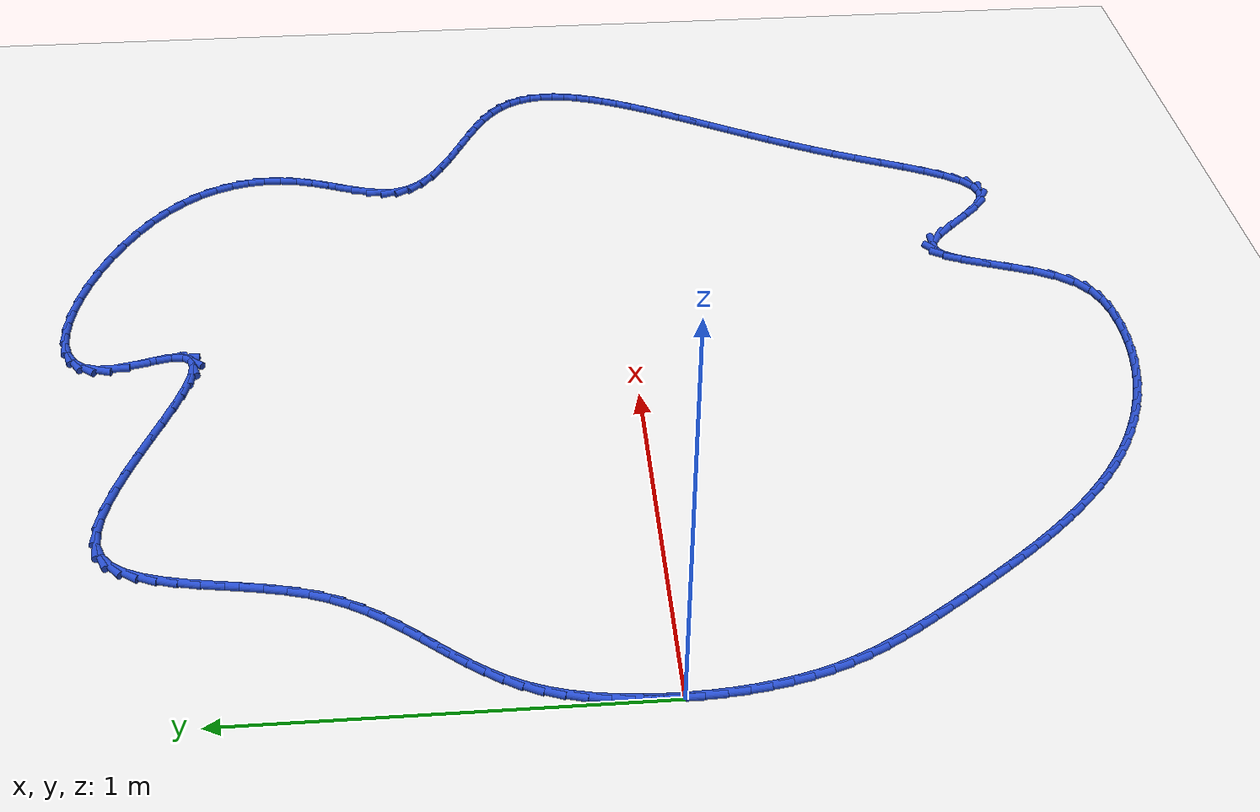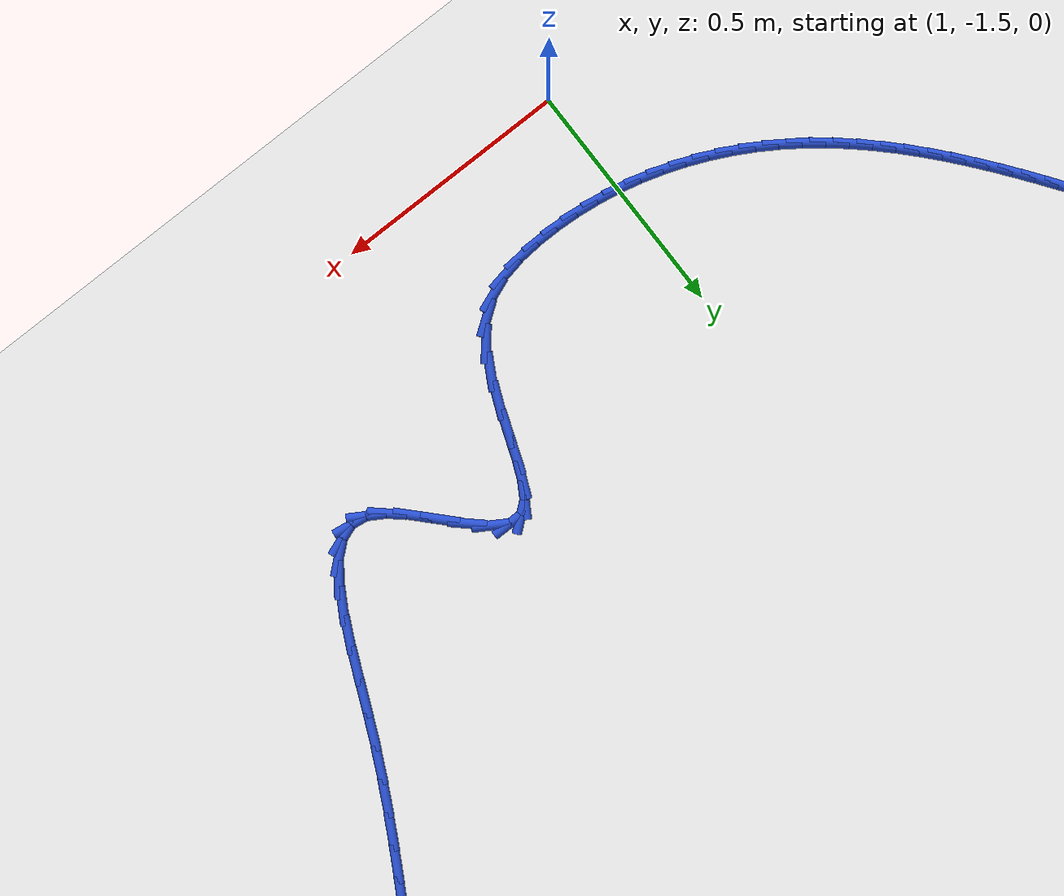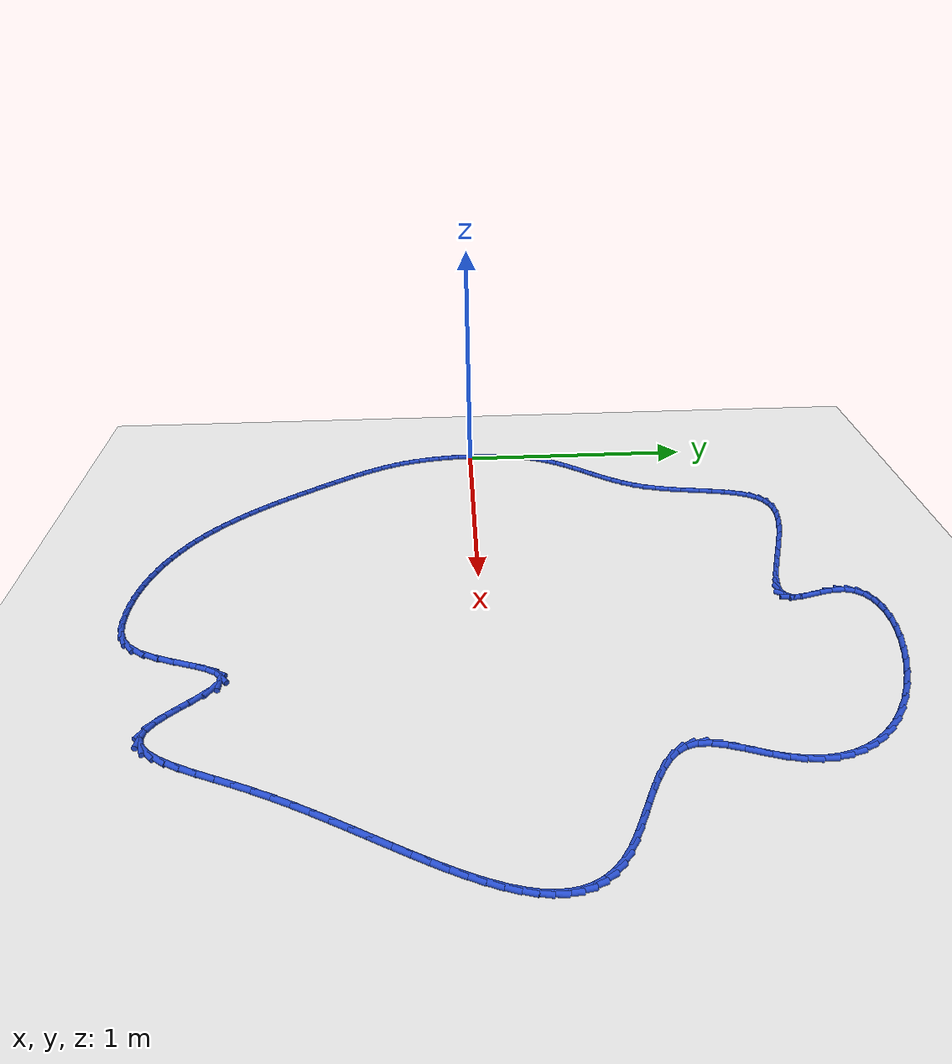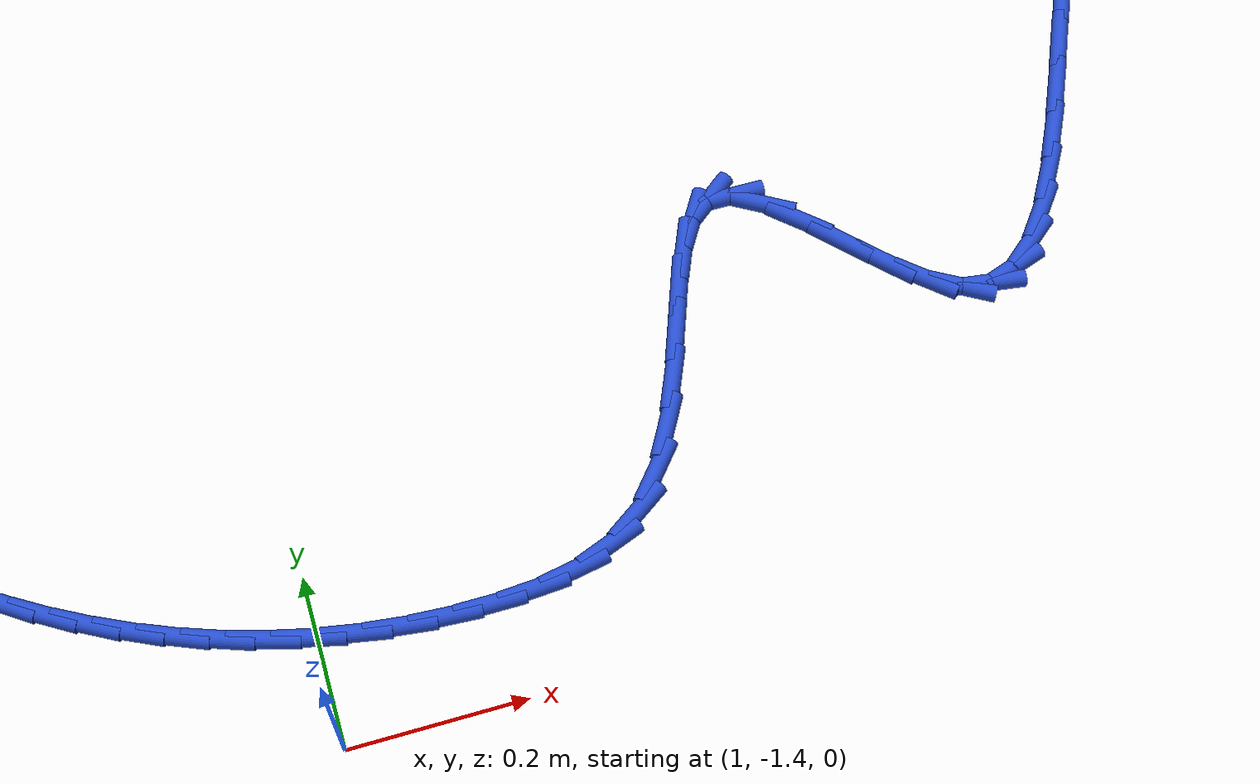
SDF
<sdf version="1.6">
 <world name="default">
  <light name="sun" type="directional">
   <pose>0 0 10 0 -0 0</pose>
   <diffuse>0.8 0.8 0.8 1</diffuse>
   <specular>0.2 0.2 0.2 1</specular>
   <attenuation>
    <range>1000</range>
    <constant>0.9</constant>
    <linear>0.01</linear>
    <quadratic>0.001</quadratic>
   </attenuation>
   <direction>-0.5 0.1 -0.9</direction>
  </light>
  <model name="ground_plane">
   <static>1</static>
   <link name="link">
    <collision name="collision">
     <geometry><plane><normal>0 0 1</normal><size>100 100</size></plane></geometry>
     <surface><friction><ode><mu>100</mu><mu2>50</mu2></ode></friction></surface>
    </collision>
    <visual name="visual">
     <cast_shadows>0</cast_shadows>
     <geometry><plane><normal>0 0 1</normal><size>100 100</size></plane></geometry>
     <material>
      <script><uri>file://media/materials/scripts/gazebo.material</uri><name>Gazebo/WhiteGlow</name></script>
     </material>
    </visual>
   </link>
  </model>
  <gravity>0 0 -9.8</gravity>
  <magnetic_field>6e-06 2.3e-05 -4.2e-05</magnetic_field>
  <atmosphere type="adiabatic"/>
  <physics name="default_physics" default="0" type="ode">
   <max_step_size>0.001</max_step_size>
   <real_time_factor>1</real_time_factor>
   <real_time_update_rate>1000</real_time_update_rate>
  </physics>
  <scene><ambient>0.4 0.4 0.4 1</ambient><background>0.7 0.7 0.7 1</background><shadows>1</shadows></scene>
  <spherical_coordinates>
   <surface_model>EARTH_WGS84</surface_model>
   <latitude_deg>0</latitude_deg>
   <longitude_deg>0</longitude_deg>
   <elevation>0</elevation>
   <heading_deg>0</heading_deg>
  </spherical_coordinates>
  <model name="line">
   <link name="link_0">
    <pose>0.0 1.3877787807814457e-17 0.01 0 1.57 1.5666232689780604</pose>
    <collision name="collision">
     <geometry><cylinder><radius>0.01</radius><length>0.08</length></cylinder></geometry>
    </collision>
    <visual name="visual">
     <material>
      <script><name>Gazebo/Blue</name><uri>file://media/materials/scripts/gazebo.material</uri></script>
     </material>
     <geometry><cylinder><radius>0.01</radius><length>0.08</length></cylinder></geometry>
    </visual>
   </link>
   <link name="link_1">
    <pose>0.0002033046258654413 0.048718099447453526 0.01 0 1.57 1.5253808544607772</pose>
    <collision name="collision">
     <geometry><cylinder><radius>0.01</radius><length>0.08</length></cylinder></geometry>
    </collision>
    <visual name="visual">
     <material>
      <script><name>Gazebo/Blue</name><uri>file://media/materials/scripts/gazebo.material</uri></script>
     </material>
     <geometry><cylinder><radius>0.01</radius><length>0.08</length></cylinder></geometry>
    </visual>
   </link>
   <link name="link_2">
    <pose>0.002415687918755517 0.09739891038097144 0.01 0 1.57 1.4777246147879786</pose>
    <collision name="collision">
     <geometry><cylinder><radius>0.01</radius><length>0.08</length></cylinder></geometry>
    </collision>
    <visual name="visual">
     <material>
      <script><name>Gazebo/Blue</name><uri>file://media/materials/scripts/gazebo.material</uri></script>
     </material>
     <geometry><cylinder><radius>0.01</radius><length>0.08</length></cylinder></geometry>
    </visual>
   </link>
   <link name="link_3">
    <pose>0.006921663336947003 0.14567305332354222 0.01 0 1.57 1.422743132023781</pose>
    <collision name="collision">
     <geometry><cylinder><radius>0.01</radius><length>0.08</length></cylinder></geometry>
    </collision>
    <visual name="visual">
     <material>
      <script><name>Gazebo/Blue</name><uri>file://media/materials/scripts/gazebo.material</uri></script>
     </material>
     <geometry><cylinder><radius>0.01</radius><length>0.08</length></cylinder></geometry>
    </visual>
   </link>
   <link name="link_4">
    <pose>0.014005744338716684 0.19317114879815447 0.01 0 1.57 1.3594145411292544</pose>
    <collision name="collision">
     <geometry><cylinder><radius>0.01</radius><length>0.08</length></cylinder></geometry>
    </collision>
    <visual name="visual">
     <material>
      <script><name>Gazebo/Blue</name><uri>file://media/materials/scripts/gazebo.material</uri></script>
     </material>
     <geometry><cylinder><radius>0.01</radius><length>0.08</length></cylinder></geometry>
    </visual>
   </link>
   <link name="link_5">
    <pose>0.023952444382341315 0.23952381732779648 0.01 0 1.57 1.2866708614399154</pose>
    <collision name="collision">
     <geometry><cylinder><radius>0.01</radius><length>0.08</length></cylinder></geometry>
    </collision>
    <visual name="visual">
     <material>
      <script><name>Gazebo/Blue</name><uri>file://media/materials/scripts/gazebo.material</uri></script>
     </material>
     <geometry><cylinder><radius>0.01</radius><length>0.08</length></cylinder></geometry>
    </visual>
   </link>
   <link name="link_6">
    <pose>0.037046276926097674 0.2843616794354568 0.01 0 1.57 1.2035244633106814</pose>
    <collision name="collision">
     <geometry><cylinder><radius>0.01</radius><length>0.08</length></cylinder></geometry>
    </collision>
    <visual name="visual">
     <material>
      <script><name>Gazebo/Blue</name><uri>file://media/materials/scripts/gazebo.material</uri></script>
     </material>
     <geometry><cylinder><radius>0.01</radius><length>0.08</length></cylinder></geometry>
    </visual>
   </link>
   <link name="link_7">
    <pose>0.05357175542826255 0.32731535564412395 0.01 0 1.57 1.1105705860418358</pose>
    <collision name="collision">
     <geometry><cylinder><radius>0.01</radius><length>0.08</length></cylinder></geometry>
    </collision>
    <visual name="visual">
     <material>
      <script><name>Gazebo/Blue</name><uri>file://media/materials/scripts/gazebo.material</uri></script>
     </material>
     <geometry><cylinder><radius>0.01</radius><length>0.08</length></cylinder></geometry>
    </visual>
   </link>
   <link name="link_8">
    <pose>0.07376855706244696 0.3680568954274267 0.01 0 1.57 1.0244880160469267</pose>
    <collision name="collision">
     <geometry><cylinder><radius>0.01</radius><length>0.08</length></cylinder></geometry>
    </collision>
    <visual name="visual">
     <material>
      <script><name>Gazebo/Blue</name><uri>file://media/materials/scripts/gazebo.material</uri></script>
     </material>
     <geometry><cylinder><radius>0.01</radius><length>0.08</length></cylinder></geometry>
    </visual>
   </link>
   <link name="link_9">
    <pose>0.09731298461001398 0.4067789090071125 0.01 0 1.57 0.9581176899792797</pose>
    <collision name="collision">
     <geometry><cylinder><radius>0.01</radius><length>0.08</length></cylinder></geometry>
    </collision>
    <visual name="visual">
     <material>
      <script><name>Gazebo/Blue</name><uri>file://media/materials/scripts/gazebo.material</uri></script>
     </material>
     <geometry><cylinder><radius>0.01</radius><length>0.08</length></cylinder></geometry>
    </visual>
   </link>
   <link name="link_10">
    <pose>0.12349680193107898 0.4440293224859489 0.01 0 1.57 0.9123637238996702</pose>
    <collision name="collision">
     <geometry><cylinder><radius>0.01</radius><length>0.08</length></cylinder></geometry>
    </collision>
    <visual name="visual">
     <material>
      <script><name>Gazebo/Blue</name><uri>file://media/materials/scripts/gazebo.material</uri></script>
     </material>
     <geometry><cylinder><radius>0.01</radius><length>0.08</length></cylinder></geometry>
    </visual>
   </link>
   <link name="link_11">
    <pose>0.15160434706261722 0.48036292346431836 0.01 0 1.57 0.8869961694170203</pose>
    <collision name="collision">
     <geometry><cylinder><radius>0.01</radius><length>0.08</length></cylinder></geometry>
    </collision>
    <visual name="visual">
     <material>
      <script><name>Gazebo/Blue</name><uri>file://media/materials/scripts/gazebo.material</uri></script>
     </material>
     <geometry><cylinder><radius>0.01</radius><length>0.08</length></cylinder></geometry>
    </visual>
   </link>
   <link name="link_12">
    <pose>0.1809199580416041 0.5163344995426039 0.01 0 1.57 0.8814499763341609</pose>
    <collision name="collision">
     <geometry><cylinder><radius>0.01</radius><length>0.08</length></cylinder></geometry>
    </collision>
    <visual name="visual">
     <material>
      <script><name>Gazebo/Blue</name><uri>file://media/materials/scripts/gazebo.material</uri></script>
     </material>
     <geometry><cylinder><radius>0.01</radius><length>0.08</length></cylinder></geometry>
    </visual>
   </link>
   <link name="link_13">
    <pose>0.21072797290501513 0.5524988383211887 0.01 0 1.57 0.8951434369867356</pose>
    <collision name="collision">
     <geometry><cylinder><radius>0.01</radius><length>0.08</length></cylinder></geometry>
    </collision>
    <visual name="visual">
     <material>
      <script><name>Gazebo/Blue</name><uri>file://media/materials/scripts/gazebo.material</uri></script>
     </material>
     <geometry><cylinder><radius>0.01</radius><length>0.08</length></cylinder></geometry>
    </visual>
   </link>
   <link name="link_14">
    <pose>0.2403127296898256 0.5894107274004555 0.01 0 1.57 0.9275436910081944</pose>
    <collision name="collision">
     <geometry><cylinder><radius>0.01</radius><length>0.08</length></cylinder></geometry>
    </collision>
    <visual name="visual">
     <material>
      <script><name>Gazebo/Blue</name><uri>file://media/materials/scripts/gazebo.material</uri></script>
     </material>
     <geometry><cylinder><radius>0.01</radius><length>0.08</length></cylinder></geometry>
    </visual>
   </link>
   <link name="link_15">
    <pose>0.26895856643301086 0.6276249543807872 0.01 0 1.57 0.9780229464078937</pose>
    <collision name="collision">
     <geometry><cylinder><radius>0.01</radius><length>0.08</length></cylinder></geometry>
    </collision>
    <visual name="visual">
     <material>
      <script><name>Gazebo/Blue</name><uri>file://media/materials/scripts/gazebo.material</uri></script>
     </material>
     <geometry><cylinder><radius>0.01</radius><length>0.08</length></cylinder></geometry>
    </visual>
   </link>
   <link name="link_16">
    <pose>0.2959498211715464 0.6676963068625665 0.01 0 1.57 1.0455522459680935</pose>
    <collision name="collision">
     <geometry><cylinder><radius>0.01</radius><length>0.08</length></cylinder></geometry>
    </collision>
    <visual name="visual">
     <material>
      <script><name>Gazebo/Blue</name><uri>file://media/materials/scripts/gazebo.material</uri></script>
     </material>
     <geometry><cylinder><radius>0.01</radius><length>0.08</length></cylinder></geometry>
    </visual>
   </link>
   <link name="link_17">
    <pose>0.32057083194240743 0.7101795724461764 0.01 0 1.57 1.1283111720617789</pose>
    <collision name="collision">
     <geometry><cylinder><radius>0.01</radius><length>0.08</length></cylinder></geometry>
    </collision>
    <visual name="visual">
     <material>
      <script><name>Gazebo/Blue</name><uri>file://media/materials/scripts/gazebo.material</uri></script>
     </material>
     <geometry><cylinder><radius>0.01</radius><length>0.08</length></cylinder></geometry>
    </visual>
   </link>
   <link name="link_18">
    <pose>0.34210593678256956 0.7556295387319998 0.01 0 1.57 1.2231473477519785</pose>
    <collision name="collision">
     <geometry><cylinder><radius>0.01</radius><length>0.08</length></cylinder></geometry>
    </collision>
    <visual name="visual">
     <material>
      <script><name>Gazebo/Blue</name><uri>file://media/materials/scripts/gazebo.material</uri></script>
     </material>
     <geometry><cylinder><radius>0.01</radius><length>0.08</length></cylinder></geometry>
    </visual>
   </link>
   <link name="link_19">
    <pose>0.3598483151359964 0.8045920638351798 0.01 0 1.57 1.3114645822825304</pose>
    <collision name="collision">
     <geometry><cylinder><radius>0.01</radius><length>0.08</length></cylinder></geometry>
    </collision>
    <visual name="visual">
     <material>
      <script><name>Gazebo/Blue</name><uri>file://media/materials/scripts/gazebo.material</uri></script>
     </material>
     <geometry><cylinder><radius>0.01</radius><length>0.08</length></cylinder></geometry>
    </visual>
   </link>
   <link name="link_20">
    <pose>0.3737409747649443 0.8569567039514656 0.01 0 1.57 1.3706537140713848</pose>
    <collision name="collision">
     <geometry><cylinder><radius>0.01</radius><length>0.08</length></cylinder></geometry>
    </collision>
    <visual name="visual">
     <material>
      <script><name>Gazebo/Blue</name><uri>file://media/materials/scripts/gazebo.material</uri></script>
     </material>
     <geometry><cylinder><radius>0.01</radius><length>0.08</length></cylinder></geometry>
    </visual>
   </link>
   <link name="link_21">
    <pose>0.38480952794594087 0.9115196258371799 0.01 0 1.57 1.40336257802225</pose>
    <collision name="collision">
     <geometry><cylinder><radius>0.01</radius><length>0.08</length></cylinder></geometry>
    </collision>
    <visual name="visual">
     <material>
      <script><name>Gazebo/Blue</name><uri>file://media/materials/scripts/gazebo.material</uri></script>
     </material>
     <geometry><cylinder><radius>0.01</radius><length>0.08</length></cylinder></geometry>
    </visual>
   </link>
   <link name="link_22">
    <pose>0.39418211680521487 0.966973444994785 0.01 0 1.57 1.4121624380151354</pose>
    <collision name="collision">
     <geometry><cylinder><radius>0.01</radius><length>0.08</length></cylinder></geometry>
    </collision>
    <visual name="visual">
     <material>
      <script><name>Gazebo/Blue</name><uri>file://media/materials/scripts/gazebo.material</uri></script>
     </material>
     <geometry><cylinder><radius>0.01</radius><length>0.08</length></cylinder></geometry>
    </visual>
   </link>
   <link name="link_23">
    <pose>0.4029868834689947 1.022010776926742 0.01 0 1.57 1.3969095403009106</pose>
    <collision name="collision">
     <geometry><cylinder><radius>0.01</radius><length>0.08</length></cylinder></geometry>
    </collision>
    <visual name="visual">
     <material>
      <script><name>Gazebo/Blue</name><uri>file://media/materials/scripts/gazebo.material</uri></script>
     </material>
     <geometry><cylinder><radius>0.01</radius><length>0.08</length></cylinder></geometry>
    </visual>
   </link>
   <link name="link_24">
    <pose>0.41235197006350854 1.0753242371355134 0.01 0 1.57 1.3544079565666542</pose>
    <collision name="collision">
     <geometry><cylinder><radius>0.01</radius><length>0.08</length></cylinder></geometry>
    </collision>
    <visual name="visual">
     <material>
      <script><name>Gazebo/Blue</name><uri>file://media/materials/scripts/gazebo.material</uri></script>
     </material>
     <geometry><cylinder><radius>0.01</radius><length>0.08</length></cylinder></geometry>
    </visual>
   </link>
   <link name="link_25">
    <pose>0.42340551871498533 1.1256064411235607 0.01 0 1.57 1.2776014932907915</pose>
    <collision name="collision">
     <geometry><cylinder><radius>0.01</radius><length>0.08</length></cylinder></geometry>
    </collision>
    <visual name="visual">
     <material>
      <script><name>Gazebo/Blue</name><uri>file://media/materials/scripts/gazebo.material</uri></script>
     </material>
     <geometry><cylinder><radius>0.01</radius><length>0.08</length></cylinder></geometry>
    </visual>
   </link>
   <link name="link_26">
    <pose>0.4372756715496534 1.1715500043933464 0.01 0 1.57 1.1545447673238585</pose>
    <collision name="collision">
     <geometry><cylinder><radius>0.01</radius><length>0.08</length></cylinder></geometry>
    </collision>
    <visual name="visual">
     <material>
      <script><name>Gazebo/Blue</name><uri>file://media/materials/scripts/gazebo.material</uri></script>
     </material>
     <geometry><cylinder><radius>0.01</radius><length>0.08</length></cylinder></geometry>
    </visual>
   </link>
   <link name="link_27">
    <pose>0.4550905706937408 1.211847542447331 0.01 0 1.57 0.9692486104632008</pose>
    <collision name="collision">
     <geometry><cylinder><radius>0.01</radius><length>0.08</length></cylinder></geometry>
    </collision>
    <visual name="visual">
     <material>
      <script><name>Gazebo/Blue</name><uri>file://media/materials/scripts/gazebo.material</uri></script>
     </material>
     <geometry><cylinder><radius>0.01</radius><length>0.08</length></cylinder></geometry>
    </visual>
   </link>
   <link name="link_28">
    <pose>0.47797835827347657 1.2451916707879775 0.01 0 1.57 0.7115925599423112</pose>
    <collision name="collision">
     <geometry><cylinder><radius>0.01</radius><length>0.08</length></cylinder></geometry>
    </collision>
    <visual name="visual">
     <material>
      <script><name>Gazebo/Blue</name><uri>file://media/materials/scripts/gazebo.material</uri></script>
     </material>
     <geometry><cylinder><radius>0.01</radius><length>0.08</length></cylinder></geometry>
    </visual>
   </link>
   <link name="link_29">
    <pose>0.507067176415089 1.2702750049177474 0.01 0 1.57 0.40276831272184777</pose>
    <collision name="collision">
     <geometry><cylinder><radius>0.01</radius><length>0.08</length></cylinder></geometry>
    </collision>
    <visual name="visual">
     <material>
      <script><name>Gazebo/Blue</name><uri>file://media/materials/scripts/gazebo.material</uri></script>
     </material>
     <geometry><cylinder><radius>0.01</radius><length>0.08</length></cylinder></geometry>
    </visual>
   </link>
   <link name="link_30">
    <pose>0.5434844601638879 1.2857909605098445 0.01 0 1.57 0.11978055243967799</pose>
    <collision name="collision">
     <geometry><cylinder><radius>0.01</radius><length>0.08</length></cylinder></geometry>
    </collision>
    <visual name="visual">
     <material>
      <script><name>Gazebo/Blue</name><uri>file://media/materials/scripts/gazebo.material</uri></script>
     </material>
     <geometry><cylinder><radius>0.01</radius><length>0.08</length></cylinder></geometry>
    </visual>
   </link>
   <link name="link_31">
    <pose>0.5877515826039983 1.2911188055024834 0.01 0 1.57 -0.06948232969701984</pose>
    <collision name="collision">
     <geometry><cylinder><radius>0.01</radius><length>0.08</length></cylinder></geometry>
    </collision>
    <visual name="visual">
     <material>
      <script><name>Gazebo/Blue</name><uri>file://media/materials/scripts/gazebo.material</uri></script>
     </material>
     <geometry><cylinder><radius>0.01</radius><length>0.08</length></cylinder></geometry>
    </visual>
   </link>
   <link name="link_32">
    <pose>0.6386784621670848 1.2875745818355941 0.01 0 1.57 -0.18952403494256415</pose>
    <collision name="collision">
     <geometry><cylinder><radius>0.01</radius><length>0.08</length></cylinder></geometry>
    </collision>
    <visual name="visual">
     <material>
      <script><name>Gazebo/Blue</name><uri>file://media/materials/scripts/gazebo.material</uri></script>
     </material>
     <geometry><cylinder><radius>0.01</radius><length>0.08</length></cylinder></geometry>
    </visual>
   </link>
   <link name="link_33">
    <pose>0.6947750609891532 1.2768137781030067 0.01 0 1.57 -0.2665521272269219</pose>
    <collision name="collision">
     <geometry><cylinder><radius>0.01</radius><length>0.08</length></cylinder></geometry>
    </collision>
    <visual name="visual">
     <material>
      <script><name>Gazebo/Blue</name><uri>file://media/materials/scripts/gazebo.material</uri></script>
     </material>
     <geometry><cylinder><radius>0.01</radius><length>0.08</length></cylinder></geometry>
    </visual>
   </link>
   <link name="link_34">
    <pose>0.75455134120621 1.2604918828985523 0.01 0 1.57 -0.3155241808932426</pose>
    <collision name="collision">
     <geometry><cylinder><radius>0.01</radius><length>0.08</length></cylinder></geometry>
    </collision>
    <visual name="visual">
     <material>
      <script><name>Gazebo/Blue</name><uri>file://media/materials/scripts/gazebo.material</uri></script>
     </material>
     <geometry><cylinder><radius>0.01</radius><length>0.08</length></cylinder></geometry>
    </visual>
   </link>
   <link name="link_35">
    <pose>0.816517264954262 1.2402643848160597 0.01 0 1.57 -0.34439700062973344</pose>
    <collision name="collision">
     <geometry><cylinder><radius>0.01</radius><length>0.08</length></cylinder></geometry>
    </collision>
    <visual name="visual">
     <material>
      <script><name>Gazebo/Blue</name><uri>file://media/materials/scripts/gazebo.material</uri></script>
     </material>
     <geometry><cylinder><radius>0.01</radius><length>0.08</length></cylinder></geometry>
    </visual>
   </link>
   <link name="link_36">
    <pose>0.8791827943693161 1.217786772449361 0.01 0 1.57 -0.3569143187581209</pose>
    <collision name="collision">
     <geometry><cylinder><radius>0.01</radius><length>0.08</length></cylinder></geometry>
    </collision>
    <visual name="visual">
     <material>
      <script><name>Gazebo/Blue</name><uri>file://media/materials/scripts/gazebo.material</uri></script>
     </material>
     <geometry><cylinder><radius>0.01</radius><length>0.08</length></cylinder></geometry>
    </visual>
   </link>
   <link name="link_37">
    <pose>0.941057891587378 1.1947145343922856 0.01 0 1.57 -0.3538095389307916</pose>
    <collision name="collision">
     <geometry><cylinder><radius>0.01</radius><length>0.08</length></cylinder></geometry>
    </collision>
    <visual name="visual">
     <material>
      <script><name>Gazebo/Blue</name><uri>file://media/materials/scripts/gazebo.material</uri></script>
     </material>
     <geometry><cylinder><radius>0.01</radius><length>0.08</length></cylinder></geometry>
    </visual>
   </link>
   <link name="link_38">
    <pose>1.0006525187444542 1.172703159238664 0.01 0 1.57 -0.3327849656271441</pose>
    <collision name="collision">
     <geometry><cylinder><radius>0.01</radius><length>0.08</length></cylinder></geometry>
    </collision>
    <visual name="visual">
     <material>
      <script><name>Gazebo/Blue</name><uri>file://media/materials/scripts/gazebo.material</uri></script>
     </material>
     <geometry><cylinder><radius>0.01</radius><length>0.08</length></cylinder></geometry>
    </visual>
   </link>
   <link name="link_39">
    <pose>1.0564766379765518 1.153408135582327 0.01 0 1.57 -0.28698941673664113</pose>
    <collision name="collision">
     <geometry><cylinder><radius>0.01</radius><length>0.08</length></cylinder></geometry>
    </collision>
    <visual name="visual">
     <material>
      <script><name>Gazebo/Blue</name><uri>file://media/materials/scripts/gazebo.material</uri></script>
     </material>
     <geometry><cylinder><radius>0.01</radius><length>0.08</length></cylinder></geometry>
    </visual>
   </link>
   <link name="link_40">
    <pose>1.107040211419677 1.1384849520171045 0.01 0 1.57 -0.20031835492136305</pose>
    <collision name="collision">
     <geometry><cylinder><radius>0.01</radius><length>0.08</length></cylinder></geometry>
    </collision>
    <visual name="visual">
     <material>
      <script><name>Gazebo/Blue</name><uri>file://media/materials/scripts/gazebo.material</uri></script>
     </material>
     <geometry><cylinder><radius>0.01</radius><length>0.08</length></cylinder></geometry>
    </visual>
   </link>
   <link name="link_41">
    <pose>1.150853201209836 1.1295890971368274 0.01 0 1.57 -0.03408734912373276</pose>
    <collision name="collision">
     <geometry><cylinder><radius>0.01</radius><length>0.08</length></cylinder></geometry>
    </collision>
    <visual name="visual">
     <material>
      <script><name>Gazebo/Blue</name><uri>file://media/materials/scripts/gazebo.material</uri></script>
     </material>
     <geometry><cylinder><radius>0.01</radius><length>0.08</length></cylinder></geometry>
    </visual>
   </link>
   <link name="link_42">
    <pose>1.1864255694830361 1.1283760595353254 0.01 0 1.57 0.3046372535998166</pose>
    <collision name="collision">
     <geometry><cylinder><radius>0.01</radius><length>0.08</length></cylinder></geometry>
    </collision>
    <visual name="visual">
     <material>
      <script><name>Gazebo/Blue</name><uri>file://media/materials/scripts/gazebo.material</uri></script>
     </material>
     <geometry><cylinder><radius>0.01</radius><length>0.08</length></cylinder></geometry>
    </visual>
   </link>
   <link name="link_43">
    <pose>1.2122672783752835 1.1365013278064298 0.01 0 1.57 0.9179314808489272</pose>
    <collision name="collision">
     <geometry><cylinder><radius>0.01</radius><length>0.08</length></cylinder></geometry>
    </collision>
    <visual name="visual">
     <material>
      <script><name>Gazebo/Blue</name><uri>file://media/materials/scripts/gazebo.material</uri></script>
     </material>
     <geometry><cylinder><radius>0.01</radius><length>0.08</length></cylinder></geometry>
    </visual>
   </link>
   <link name="link_44">
    <pose>1.2268882900225841 1.1556203905439701 0.01 0 1.57 1.509342696568505</pose>
    <collision name="collision">
     <geometry><cylinder><radius>0.01</radius><length>0.08</length></cylinder></geometry>
    </collision>
    <visual name="visual">
     <material>
      <script><name>Gazebo/Blue</name><uri>file://media/materials/scripts/gazebo.material</uri></script>
     </material>
     <geometry><cylinder><radius>0.01</radius><length>0.08</length></cylinder></geometry>
    </visual>
   </link>
   <link name="link_45">
    <pose>1.2288407437148205 1.1873515546843953 0.01 0 1.57 -1.3631857798975189</pose>
    <collision name="collision">
     <geometry><cylinder><radius>0.01</radius><length>0.08</length></cylinder></geometry>
    </collision>
    <visual name="visual">
     <material>
      <script><name>Gazebo/Blue</name><uri>file://media/materials/scripts/gazebo.material</uri></script>
     </material>
     <geometry><cylinder><radius>0.01</radius><length>0.08</length></cylinder></geometry>
    </visual>
   </link>
   <link name="link_46">
    <pose>1.2197252214525915 1.2306257444936068 0.01 0 1.57 -1.302869429223979</pose>
    <collision name="collision">
     <geometry><cylinder><radius>0.01</radius><length>0.08</length></cylinder></geometry>
    </collision>
    <visual name="visual">
     <material>
      <script><name>Gazebo/Blue</name><uri>file://media/materials/scripts/gazebo.material</uri></script>
     </material>
     <geometry><cylinder><radius>0.01</radius><length>0.08</length></cylinder></geometry>
    </visual>
   </link>
   <link name="link_47">
    <pose>1.2061919550621625 1.2799223190543665 0.01 0 1.57 -1.3549696174495471</pose>
    <collision name="collision">
     <geometry><cylinder><radius>0.01</radius><length>0.08</length></cylinder></geometry>
    </collision>
    <visual name="visual">
     <material>
      <script><name>Gazebo/Blue</name><uri>file://media/materials/scripts/gazebo.material</uri></script>
     </material>
     <geometry><cylinder><radius>0.01</radius><length>0.08</length></cylinder></geometry>
    </visual>
   </link>
   <link name="link_48">
    <pose>1.1953658365319724 1.3293021964238787 0.01 0 1.57 -1.543472222563412</pose>
    <collision name="collision">
     <geometry><cylinder><radius>0.01</radius><length>0.08</length></cylinder></geometry>
    </collision>
    <visual name="visual">
     <material>
      <script><name>Gazebo/Blue</name><uri>file://media/materials/scripts/gazebo.material</uri></script>
     </material>
     <geometry><cylinder><radius>0.01</radius><length>0.08</length></cylinder></geometry>
    </visual>
   </link>
   <link name="link_49">
    <pose>1.194172181575558 1.3729763775766313 0.01 0 1.57 1.2639051228521465</pose>
    <collision name="collision">
     <geometry><cylinder><radius>0.01</radius><length>0.08</length></cylinder></geometry>
    </collision>
    <visual name="visual">
     <material>
      <script><name>Gazebo/Blue</name><uri>file://media/materials/scripts/gazebo.material</uri></script>
     </material>
     <geometry><cylinder><radius>0.01</radius><length>0.08</length></cylinder></geometry>
    </visual>
   </link>
   <link name="link_50">
    <pose>1.205364224683296 1.4082933011480983 0.01 0 1.57 0.8837807894317415</pose>
    <collision name="collision">
     <geometry><cylinder><radius>0.01</radius><length>0.08</length></cylinder></geometry>
    </collision>
    <visual name="visual">
     <material>
      <script><name>Gazebo/Blue</name><uri>file://media/materials/scripts/gazebo.material</uri></script>
     </material>
     <geometry><cylinder><radius>0.01</radius><length>0.08</length></cylinder></geometry>
    </visual>
   </link>
   <link name="link_51">
    <pose>1.227743006416404 1.4355734864724743 0.01 0 1.57 0.5484690647117576</pose>
    <collision name="collision">
     <geometry><cylinder><radius>0.01</radius><length>0.08</length></cylinder></geometry>
    </collision>
    <visual name="visual">
     <material>
      <script><name>Gazebo/Blue</name><uri>file://media/materials/scripts/gazebo.material</uri></script>
     </material>
     <geometry><cylinder><radius>0.01</radius><length>0.08</length></cylinder></geometry>
    </visual>
   </link>
   <link name="link_52">
    <pose>1.2599540089391188 1.4552544340132947 0.01 0 1.57 0.2984901426879694</pose>
    <collision name="collision">
     <geometry><cylinder><radius>0.01</radius><length>0.08</length></cylinder></geometry>
    </collision>
    <visual name="visual">
     <material>
      <script><name>Gazebo/Blue</name><uri>file://media/materials/scripts/gazebo.material</uri></script>
     </material>
     <geometry><cylinder><radius>0.01</radius><length>0.08</length></cylinder></geometry>
    </visual>
   </link>
   <link name="link_53">
    <pose>1.3006427144156738 1.4677736442340934 0.01 0 1.57 0.12061527283436092</pose>
    <collision name="collision">
     <geometry><cylinder><radius>0.01</radius><length>0.08</length></cylinder></geometry>
    </collision>
    <visual name="visual">
     <material>
      <script><name>Gazebo/Blue</name><uri>file://media/materials/scripts/gazebo.material</uri></script>
     </material>
     <geometry><cylinder><radius>0.01</radius><length>0.08</length></cylinder></geometry>
    </visual>
   </link>
   <link name="link_54">
    <pose>1.3484546050103041 1.4735686175984053 0.01 0 1.57 -0.00917775478246893</pose>
    <collision name="collision">
     <geometry><cylinder><radius>0.01</radius><length>0.08</length></cylinder></geometry>
    </collision>
    <visual name="visual">
     <material>
      <script><name>Gazebo/Blue</name><uri>file://media/materials/scripts/gazebo.material</uri></script>
     </material>
     <geometry><cylinder><radius>0.01</radius><length>0.08</length></cylinder></geometry>
    </visual>
   </link>
   <link name="link_55">
    <pose>1.4020351628872454 1.4730768545697648 0.01 0 1.57 -0.10890494523205782</pose>
    <collision name="collision">
     <geometry><cylinder><radius>0.01</radius><length>0.08</length></cylinder></geometry>
    </collision>
    <visual name="visual">
     <material>
      <script><name>Gazebo/Blue</name><uri>file://media/materials/scripts/gazebo.material</uri></script>
     </material>
     <geometry><cylinder><radius>0.01</radius><length>0.08</length></cylinder></geometry>
    </visual>
   </link>
   <link name="link_56">
    <pose>1.4600298702107315 1.4667358556117058 0.01 0 1.57 -0.19017016413349755</pose>
    <collision name="collision">
     <geometry><cylinder><radius>0.01</radius><length>0.08</length></cylinder></geometry>
    </collision>
    <visual name="visual">
     <material>
      <script><name>Gazebo/Blue</name><uri>file://media/materials/scripts/gazebo.material</uri></script>
     </material>
     <geometry><cylinder><radius>0.01</radius><length>0.08</length></cylinder></geometry>
    </visual>
   </link>
   <link name="link_57">
    <pose>1.5210842091449983 1.4549831211877642 0.01 0 1.57 -0.2604702192928912</pose>
    <collision name="collision">
     <geometry><cylinder><radius>0.01</radius><length>0.08</length></cylinder></geometry>
    </collision>
    <visual name="visual">
     <material>
      <script><name>Gazebo/Blue</name><uri>file://media/materials/scripts/gazebo.material</uri></script>
     </material>
     <geometry><cylinder><radius>0.01</radius><length>0.08</length></cylinder></geometry>
    </visual>
   </link>
   <link name="link_58">
    <pose>1.583843661854281 1.438256151761473 0.01 0 1.57 -0.32498455611469085</pose>
    <collision name="collision">
     <geometry><cylinder><radius>0.01</radius><length>0.08</length></cylinder></geometry>
    </collision>
    <visual name="visual">
     <material>
      <script><name>Gazebo/Blue</name><uri>file://media/materials/scripts/gazebo.material</uri></script>
     </material>
     <geometry><cylinder><radius>0.01</radius><length>0.08</length></cylinder></geometry>
    </visual>
   </link>
   <link name="link_59">
    <pose>1.6469537105028131 1.4169924477963676 0.01 0 1.57 -0.3877100997034499</pose>
    <collision name="collision">
     <geometry><cylinder><radius>0.01</radius><length>0.08</length></cylinder></geometry>
    </collision>
    <visual name="visual">
     <material>
      <script><name>Gazebo/Blue</name><uri>file://media/materials/scripts/gazebo.material</uri></script>
     </material>
     <geometry><cylinder><radius>0.01</radius><length>0.08</length></cylinder></geometry>
    </visual>
   </link>
   <link name="link_60">
    <pose>1.7090598372548311 1.3916295097559819 0.01 0 1.57 -0.45221299297175904</pose>
    <collision name="collision">
     <geometry><cylinder><radius>0.01</radius><length>0.08</length></cylinder></geometry>
    </collision>
    <visual name="visual">
     <material>
      <script><name>Gazebo/Blue</name><uri>file://media/materials/scripts/gazebo.material</uri></script>
     </material>
     <geometry><cylinder><radius>0.01</radius><length>0.08</length></cylinder></geometry>
    </visual>
   </link>
   <link name="link_61">
    <pose>1.7688075242745689 1.3626048381038514 0.01 0 1.57 -0.5222222685306123</pose>
    <collision name="collision">
     <geometry><cylinder><radius>0.01</radius><length>0.08</length></cylinder></geometry>
    </collision>
    <visual name="visual">
     <material>
      <script><name>Gazebo/Blue</name><uri>file://media/materials/scripts/gazebo.material</uri></script>
     </material>
     <geometry><cylinder><radius>0.01</radius><length>0.08</length></cylinder></geometry>
    </visual>
   </link>
   <link name="link_62">
    <pose>1.8248422537262612 1.3303559333035095 0.01 0 1.57 -0.602229392419917</pose>
    <collision name="collision">
     <geometry><cylinder><radius>0.01</radius><length>0.08</length></cylinder></geometry>
    </collision>
    <visual name="visual">
     <material>
      <script><name>Gazebo/Blue</name><uri>file://media/materials/scripts/gazebo.material</uri></script>
     </material>
     <geometry><cylinder><radius>0.01</radius><length>0.08</length></cylinder></geometry>
    </visual>
   </link>
   <link name="link_63">
    <pose>1.8758095077741448 1.2953202958184913 0.01 0 1.57 -0.6974812354569768</pose>
    <collision name="collision">
     <geometry><cylinder><radius>0.01</radius><length>0.08</length></cylinder></geometry>
    </collision>
    <visual name="visual">
     <material>
      <script><name>Gazebo/Blue</name><uri>file://media/materials/scripts/gazebo.material</uri></script>
     </material>
     <geometry><cylinder><radius>0.01</radius><length>0.08</length></cylinder></geometry>
    </visual>
   </link>
   <link name="link_64">
    <pose>1.9204390569906598 1.2579211001896966 0.01 0 1.57 -0.806347410863595</pose>
    <collision name="collision">
     <geometry><cylinder><radius>0.01</radius><length>0.08</length></cylinder></geometry>
    </collision>
    <visual name="visual">
     <material>
      <script><name>Gazebo/Blue</name><uri>file://media/materials/scripts/gazebo.material</uri></script>
     </material>
     <geometry><cylinder><radius>0.01</radius><length>0.08</length></cylinder></geometry>
    </visual>
   </link>
   <link name="link_65">
    <pose>1.9583009041307067 1.2184387124568747 0.01 0 1.57 -0.9254235962651746</pose>
    <collision name="collision">
     <geometry><cylinder><radius>0.01</radius><length>0.08</length></cylinder></geometry>
    </collision>
    <visual name="visual">
     <material>
      <script><name>Gazebo/Blue</name><uri>file://media/materials/scripts/gazebo.material</uri></script>
     </material>
     <geometry><cylinder><radius>0.01</radius><length>0.08</length></cylinder></geometry>
    </visual>
   </link>
   <link name="link_66">
    <pose>1.9894474519612113 1.177071508438366 0.01 0 1.57 -1.0536353584999212</pose>
    <collision name="collision">
     <geometry><cylinder><radius>0.01</radius><length>0.08</length></cylinder></geometry>
    </collision>
    <visual name="visual">
     <material>
      <script><name>Gazebo/Blue</name><uri>file://media/materials/scripts/gazebo.material</uri></script>
     </material>
     <geometry><cylinder><radius>0.01</radius><length>0.08</length></cylinder></geometry>
    </visual>
   </link>
   <link name="link_67">
    <pose>2.0139368420238357 1.1340168885723312 0.01 0 1.57 -1.1888872692599786</pose>
    <collision name="collision">
     <geometry><cylinder><radius>0.01</radius><length>0.08</length></cylinder></geometry>
    </collision>
    <visual name="visual">
     <material>
      <script><name>Gazebo/Blue</name><uri>file://media/materials/scripts/gazebo.material</uri></script>
     </material>
     <geometry><cylinder><radius>0.01</radius><length>0.08</length></cylinder></geometry>
    </visual>
   </link>
   <link name="link_68">
    <pose>2.031827215860241 1.0894722532969296 0.01 0 1.57 -1.3280737308367965</pose>
    <collision name="collision">
     <geometry><cylinder><radius>0.01</radius><length>0.08</length></cylinder></geometry>
    </collision>
    <visual name="visual">
     <material>
      <script><name>Gazebo/Blue</name><uri>file://media/materials/scripts/gazebo.material</uri></script>
     </material>
     <geometry><cylinder><radius>0.01</radius><length>0.08</length></cylinder></geometry>
    </visual>
   </link>
   <link name="link_69">
    <pose>2.04317671501209 1.0436350030503212 0.01 0 1.57 -1.4674684187488845</pose>
    <collision name="collision">
     <geometry><cylinder><radius>0.01</radius><length>0.08</length></cylinder></geometry>
    </collision>
    <visual name="visual">
     <material>
      <script><name>Gazebo/Blue</name><uri>file://media/materials/scripts/gazebo.material</uri></script>
     </material>
     <geometry><cylinder><radius>0.01</radius><length>0.08</length></cylinder></geometry>
    </visual>
   </link>
   <link name="link_70">
    <pose>2.0480434810210433 0.9967025382706665 0.01 0 1.57 1.5382379739220828</pose>
    <collision name="collision">
     <geometry><cylinder><radius>0.01</radius><length>0.08</length></cylinder></geometry>
    </collision>
    <visual name="visual">
     <material>
      <script><name>Gazebo/Blue</name><uri>file://media/materials/scripts/gazebo.material</uri></script>
     </material>
     <geometry><cylinder><radius>0.01</radius><length>0.08</length></cylinder></geometry>
    </visual>
   </link>
   <link name="link_71">
    <pose>2.046485655428763 0.9488722593961243 0.01 0 1.57 1.4089408867401596</pose>
    <collision name="collision">
     <geometry><cylinder><radius>0.01</radius><length>0.08</length></cylinder></geometry>
    </collision>
    <visual name="visual">
     <material>
      <script><name>Gazebo/Blue</name><uri>file://media/materials/scripts/gazebo.material</uri></script>
     </material>
     <geometry><cylinder><radius>0.01</radius><length>0.08</length></cylinder></geometry>
    </visual>
   </link>
   <link name="link_72">
    <pose>2.03856137977691 0.9003415668648556 0.01 0 1.57 1.2935672476214564</pose>
    <collision name="collision">
     <geometry><cylinder><radius>0.01</radius><length>0.08</length></cylinder></geometry>
    </collision>
    <visual name="visual">
     <material>
      <script><name>Gazebo/Blue</name><uri>file://media/materials/scripts/gazebo.material</uri></script>
     </material>
     <geometry><cylinder><radius>0.01</radius><length>0.08</length></cylinder></geometry>
    </visual>
   </link>
   <link name="link_73">
    <pose>2.0246238695339693 0.851361831211347 0.01 0 1.57 1.224349799349156</pose>
    <collision name="collision">
     <geometry><cylinder><radius>0.01</radius><length>0.08</length></cylinder></geometry>
    </collision>
    <visual name="visual">
     <material>
      <script><name>Gazebo/Blue</name><uri>file://media/materials/scripts/gazebo.material</uri></script>
     </material>
     <geometry><cylinder><radius>0.01</radius><length>0.08</length></cylinder></geometry>
    </visual>
   </link>
   <link name="link_74">
    <pose>2.00700087104609 0.802545571861877 0.01 0 1.57 1.2081696734709182</pose>
    <collision name="collision">
     <geometry><cylinder><radius>0.01</radius><length>0.08</length></cylinder></geometry>
    </collision>
    <visual name="visual">
     <material>
      <script><name>Gazebo/Blue</name><uri>file://media/materials/scripts/gazebo.material</uri></script>
     </material>
     <geometry><cylinder><radius>0.01</radius><length>0.08</length></cylinder></geometry>
    </visual>
   </link>
   <link name="link_75">
    <pose>1.9888304013260205 0.7546535096998934 0.01 0 1.57 1.2456366924832711</pose>
    <collision name="collision">
     <geometry><cylinder><radius>0.01</radius><length>0.08</length></cylinder></geometry>
    </collision>
    <visual name="visual">
     <material>
      <script><name>Gazebo/Blue</name><uri>file://media/materials/scripts/gazebo.material</uri></script>
     </material>
     <geometry><cylinder><radius>0.01</radius><length>0.08</length></cylinder></geometry>
    </visual>
   </link>
   <link name="link_76">
    <pose>1.9732529458777097 0.708446817104878 0.01 0 1.57 1.3495270877420338</pose>
    <collision name="collision">
     <geometry><cylinder><radius>0.01</radius><length>0.08</length></cylinder></geometry>
    </collision>
    <visual name="visual">
     <material>
      <script><name>Gazebo/Blue</name><uri>file://media/materials/scripts/gazebo.material</uri></script>
     </material>
     <geometry><cylinder><radius>0.01</radius><length>0.08</length></cylinder></geometry>
    </visual>
   </link>
   <link name="link_77">
    <pose>1.9634089902051066 0.6646866664563114 0.01 0 1.57 1.546881968835788</pose>
    <collision name="collision">
     <geometry><cylinder><radius>0.01</radius><length>0.08</length></cylinder></geometry>
    </collision>
    <visual name="visual">
     <material>
      <script><name>Gazebo/Blue</name><uri>file://media/materials/scripts/gazebo.material</uri></script>
     </material>
     <geometry><cylinder><radius>0.01</radius><length>0.08</length></cylinder></geometry>
    </visual>
   </link>
   <link name="link_78">
    <pose>1.96243901981216 0.6241342301336769 0.01 0 1.57 -1.2881896681887413</pose>
    <collision name="collision">
     <geometry><cylinder><radius>0.01</radius><length>0.08</length></cylinder></geometry>
    </collision>
    <visual name="visual">
     <material>
      <script><name>Gazebo/Blue</name><uri>file://media/materials/scripts/gazebo.material</uri></script>
     </material>
     <geometry><cylinder><radius>0.01</radius><length>0.08</length></cylinder></geometry>
    </visual>
   </link>
   <link name="link_79">
    <pose>1.973092229551928 0.5874469258354396 0.01 0 1.57 -0.9852000687157021</pose>
    <collision name="collision">
     <geometry><cylinder><radius>0.01</radius><length>0.08</length></cylinder></geometry>
    </collision>
    <visual name="visual">
     <material>
      <script><name>Gazebo/Blue</name><uri>file://media/materials/scripts/gazebo.material</uri></script>
     </material>
     <geometry><cylinder><radius>0.01</radius><length>0.08</length></cylinder></geometry>
    </visual>
   </link>
   <link name="link_80">
    <pose>1.9949762356224519 0.5544491498462002 0.01 0 1.57 -0.7637050661568695</pose>
    <collision name="collision">
     <geometry><cylinder><radius>0.01</radius><length>0.08</length></cylinder></geometry>
    </collision>
    <visual name="visual">
     <material>
      <script><name>Gazebo/Blue</name><uri>file://media/materials/scripts/gazebo.material</uri></script>
     </material>
     <geometry><cylinder><radius>0.01</radius><length>0.08</length></cylinder></geometry>
    </visual>
   </link>
   <link name="link_81">
    <pose>2.0261865796134777 0.5245643565463814 0.01 0 1.57 -0.6161809994394511</pose>
    <collision name="collision">
     <geometry><cylinder><radius>0.01</radius><length>0.08</length></cylinder></geometry>
    </collision>
    <visual name="visual">
     <material>
      <script><name>Gazebo/Blue</name><uri>file://media/materials/scripts/gazebo.material</uri></script>
     </material>
     <geometry><cylinder><radius>0.01</radius><length>0.08</length></cylinder></geometry>
    </visual>
   </link>
   <link name="link_82">
    <pose>2.0648091353923106 0.4972134368218371 0.01 0 1.57 -0.5222904254570231</pose>
    <collision name="collision">
     <geometry><cylinder><radius>0.01</radius><length>0.08</length></cylinder></geometry>
    </collision>
    <visual name="visual">
     <material>
      <script><name>Gazebo/Blue</name><uri>file://media/materials/scripts/gazebo.material</uri></script>
     </material>
     <geometry><cylinder><radius>0.01</radius><length>0.08</length></cylinder></geometry>
    </visual>
   </link>
   <link name="link_83">
    <pose>2.1089297768262583 0.47181728155842156 0.01 0 1.57 -0.4664643118954944</pose>
    <collision name="collision">
     <geometry><cylinder><radius>0.01</radius><length>0.08</length></cylinder></geometry>
    </collision>
    <visual name="visual">
     <material>
      <script><name>Gazebo/Blue</name><uri>file://media/materials/scripts/gazebo.material</uri></script>
     </material>
     <geometry><cylinder><radius>0.01</radius><length>0.08</length></cylinder></geometry>
    </visual>
   </link>
   <link name="link_84">
    <pose>2.1566343777826256 0.4477967816419896 0.01 0 1.57 -0.43965894056084803</pose>
    <collision name="collision">
     <geometry><cylinder><radius>0.01</radius><length>0.08</length></cylinder></geometry>
    </collision>
    <visual name="visual">
     <material>
      <script><name>Gazebo/Blue</name><uri>file://media/materials/scripts/gazebo.material</uri></script>
     </material>
     <geometry><cylinder><radius>0.01</radius><length>0.08</length></cylinder></geometry>
    </visual>
   </link>
   <link name="link_85">
    <pose>2.206008812128722 0.42457282795839507 0.01 0 1.57 -0.4379487183296495</pose>
    <collision name="collision">
     <geometry><cylinder><radius>0.01</radius><length>0.08</length></cylinder></geometry>
    </collision>
    <visual name="visual">
     <material>
      <script><name>Gazebo/Blue</name><uri>file://media/materials/scripts/gazebo.material</uri></script>
     </material>
     <geometry><cylinder><radius>0.01</radius><length>0.08</length></cylinder></geometry>
    </visual>
   </link>
   <link name="link_86">
    <pose>2.255138953731849 0.40156631139349286 0.01 0 1.57 -0.461641454257462</pose>
    <collision name="collision">
     <geometry><cylinder><radius>0.01</radius><length>0.08</length></cylinder></geometry>
    </collision>
    <visual name="visual">
     <material>
      <script><name>Gazebo/Blue</name><uri>file://media/materials/scripts/gazebo.material</uri></script>
     </material>
     <geometry><cylinder><radius>0.01</radius><length>0.08</length></cylinder></geometry>
    </visual>
   </link>
   <link name="link_87">
    <pose>2.302110676459318 0.3781981228331372 0.01 0 1.57 -0.5155390493074001</pose>
    <collision name="collision">
     <geometry><cylinder><radius>0.01</radius><length>0.08</length></cylinder></geometry>
    </collision>
    <visual name="visual">
     <material>
      <script><name>Gazebo/Blue</name><uri>file://media/materials/scripts/gazebo.material</uri></script>
     </material>
     <geometry><cylinder><radius>0.01</radius><length>0.08</length></cylinder></geometry>
    </visual>
   </link>
   <link name="link_88">
    <pose>2.3450098541784334 0.35388915316318226 0.01 0 1.57 -0.610193835177698</pose>
    <collision name="collision">
     <geometry><cylinder><radius>0.01</radius><length>0.08</length></cylinder></geometry>
    </collision>
    <visual name="visual">
     <material>
      <script><name>Gazebo/Blue</name><uri>file://media/materials/scripts/gazebo.material</uri></script>
     </material>
     <geometry><cylinder><radius>0.01</radius><length>0.08</length></cylinder></geometry>
    </visual>
   </link>
   <link name="link_89">
    <pose>2.3819424281879633 0.328065623278978 0.01 0 1.57 -0.7452869655760094</pose>
    <collision name="collision">
     <geometry><cylinder><radius>0.01</radius><length>0.08</length></cylinder></geometry>
    </collision>
    <visual name="visual">
     <material>
      <script><name>Gazebo/Blue</name><uri>file://media/materials/scripts/gazebo.material</uri></script>
     </material>
     <geometry><cylinder><radius>0.01</radius><length>0.08</length></cylinder></geometry>
    </visual>
   </link>
   <link name="link_90">
    <pose>2.411925951326789 0.30039588262998235 0.01 0 1.57 -0.9020865906434767</pose>
    <collision name="collision">
     <geometry><cylinder><radius>0.01</radius><length>0.08</length></cylinder></geometry>
    </collision>
    <visual name="visual">
     <material>
      <script><name>Gazebo/Blue</name><uri>file://media/materials/scripts/gazebo.material</uri></script>
     </material>
     <geometry><cylinder><radius>0.01</radius><length>0.08</length></cylinder></geometry>
    </visual>
   </link>
   <link name="link_91">
    <pose>2.4352444293134257 0.27088465684245794 0.01 0 1.57 -1.0727909337233112</pose>
    <collision name="collision">
     <geometry><cylinder><radius>0.01</radius><length>0.08</length></cylinder></geometry>
    </collision>
    <visual name="visual">
     <material>
      <script><name>Gazebo/Blue</name><uri>file://media/materials/scripts/gazebo.material</uri></script>
     </material>
     <geometry><cylinder><radius>0.01</radius><length>0.08</length></cylinder></geometry>
    </visual>
   </link>
   <link name="link_92">
    <pose>2.4522753168598155 0.23956149205959243 0.01 0 1.57 -1.2467214031221872</pose>
    <collision name="collision">
     <geometry><cylinder><radius>0.01</radius><length>0.08</length></cylinder></geometry>
    </collision>
    <visual name="visual">
     <material>
      <script><name>Gazebo/Blue</name><uri>file://media/materials/scripts/gazebo.material</uri></script>
     </material>
     <geometry><cylinder><radius>0.01</radius><length>0.08</length></cylinder></geometry>
    </visual>
   </link>
   <link name="link_93">
    <pose>2.4633960686779015 0.20645593442457544 0.01 0 1.57 -1.4118410546046563</pose>
    <collision name="collision">
     <geometry><cylinder><radius>0.01</radius><length>0.08</length></cylinder></geometry>
    </collision>
    <visual name="visual">
     <material>
      <script><name>Gazebo/Blue</name><uri>file://media/materials/scripts/gazebo.material</uri></script>
     </material>
     <geometry><cylinder><radius>0.01</radius><length>0.08</length></cylinder></geometry>
    </visual>
   </link>
   <link name="link_94">
    <pose>2.468984139479624 0.17159753008059456 0.01 0 1.57 -1.5589646119994758</pose>
    <collision name="collision">
     <geometry><cylinder><radius>0.01</radius><length>0.08</length></cylinder></geometry>
    </collision>
    <visual name="visual">
     <material>
      <script><name>Gazebo/Blue</name><uri>file://media/materials/scripts/gazebo.material</uri></script>
     </material>
     <geometry><cylinder><radius>0.01</radius><length>0.08</length></cylinder></geometry>
    </visual>
   </link>
   <link name="link_95">
    <pose>2.4694169839769264 0.13501582517083807 0.01 0 1.57 1.4577628848935802</pose>
    <collision name="collision">
     <geometry><cylinder><radius>0.01</radius><length>0.08</length></cylinder></geometry>
    </collision>
    <visual name="visual">
     <material>
      <script><name>Gazebo/Blue</name><uri>file://media/materials/scripts/gazebo.material</uri></script>
     </material>
     <geometry><cylinder><radius>0.01</radius><length>0.08</length></cylinder></geometry>
    </visual>
   </link>
   <link name="link_96">
    <pose>2.465072056881749 0.09674036583849423 0.01 0 1.57 1.3552369271446367</pose>
    <collision name="collision">
     <geometry><cylinder><radius>0.01</radius><length>0.08</length></cylinder></geometry>
    </collision>
    <visual name="visual">
     <material>
      <script><name>Gazebo/Blue</name><uri>file://media/materials/scripts/gazebo.material</uri></script>
     </material>
     <geometry><cylinder><radius>0.01</radius><length>0.08</length></cylinder></geometry>
    </visual>
   </link>
   <link name="link_97">
    <pose>2.456326812906034 0.056800698226751364 0.01 0 1.57 1.2728247302434434</pose>
    <collision name="collision">
     <geometry><cylinder><radius>0.01</radius><length>0.08</length></cylinder></geometry>
    </collision>
    <visual name="visual">
     <material>
      <script><name>Gazebo/Blue</name><uri>file://media/materials/scripts/gazebo.material</uri></script>
     </material>
     <geometry><cylinder><radius>0.01</radius><length>0.08</length></cylinder></geometry>
    </visual>
   </link>
   <link name="link_98">
    <pose>2.4435587067617233 0.015226368478796902 0.01 0 1.57 1.2075415752916292</pose>
    <collision name="collision">
     <geometry><cylinder><radius>0.01</radius><length>0.08</length></cylinder></geometry>
    </collision>
    <visual name="visual">
     <material>
      <script><name>Gazebo/Blue</name><uri>file://media/materials/scripts/gazebo.material</uri></script>
     </material>
     <geometry><cylinder><radius>0.01</radius><length>0.08</length></cylinder></geometry>
    </visual>
   </link>
   <link name="link_99">
    <pose>2.4271451931607584 -0.02795307726217937 0.01 0 1.57 1.1564905294754766</pose>
    <collision name="collision">
     <geometry><cylinder><radius>0.01</radius><length>0.08</length></cylinder></geometry>
    </collision>
    <visual name="visual">
     <material>
      <script><name>Gazebo/Blue</name><uri>file://media/materials/scripts/gazebo.material</uri></script>
     </material>
     <geometry><cylinder><radius>0.01</radius><length>0.08</length></cylinder></geometry>
    </visual>
   </link>
   <link name="link_100">
    <pose>2.4074637268150827 -0.07270809285298975 0.01 0 1.57 1.117195005848099</pose>
    <collision name="collision">
     <geometry><cylinder><radius>0.01</radius><length>0.08</length></cylinder></geometry>
    </collision>
    <visual name="visual">
     <material>
      <script><name>Gazebo/Blue</name><uri>file://media/materials/scripts/gazebo.material</uri></script>
     </material>
     <geometry><cylinder><radius>0.01</radius><length>0.08</length></cylinder></geometry>
    </visual>
   </link>
   <link name="link_101">
    <pose>2.3848917624366366 -0.11900913215044608 0.01 0 1.57 1.0876639595951156</pose>
    <collision name="collision">
     <geometry><cylinder><radius>0.01</radius><length>0.08</length></cylinder></geometry>
    </collision>
    <visual name="visual">
     <material>
      <script><name>Gazebo/Blue</name><uri>file://media/materials/scripts/gazebo.material</uri></script>
     </material>
     <geometry><cylinder><radius>0.01</radius><length>0.08</length></cylinder></geometry>
    </visual>
   </link>
   <link name="link_102">
    <pose>2.359806754737362 -0.16682664901136002 0.01 0 1.57 1.0663483174347654</pose>
    <collision name="collision">
     <geometry><cylinder><radius>0.01</radius><length>0.08</length></cylinder></geometry>
    </collision>
    <visual name="visual">
     <material>
      <script><name>Gazebo/Blue</name><uri>file://media/materials/scripts/gazebo.material</uri></script>
     </material>
     <geometry><cylinder><radius>0.01</radius><length>0.08</length></cylinder></geometry>
    </visual>
   </link>
   <link name="link_103">
    <pose>2.3325861584292005 -0.21613109729254437 0.01 0 1.57 1.0520666024061351</pose>
    <collision name="collision">
     <geometry><cylinder><radius>0.01</radius><length>0.08</length></cylinder></geometry>
    </collision>
    <visual name="visual">
     <material>
      <script><name>Gazebo/Blue</name><uri>file://media/materials/scripts/gazebo.material</uri></script>
     </material>
     <geometry><cylinder><radius>0.01</radius><length>0.08</length></cylinder></geometry>
    </visual>
   </link>
   <link name="link_104">
    <pose>2.303607428224095 -0.2668929308508089 0.01 0 1.57 1.0439317083903372</pose>
    <collision name="collision">
     <geometry><cylinder><radius>0.01</radius><length>0.08</length></cylinder></geometry>
    </collision>
    <visual name="visual">
     <material>
      <script><name>Gazebo/Blue</name><uri>file://media/materials/scripts/gazebo.material</uri></script>
     </material>
     <geometry><cylinder><radius>0.01</radius><length>0.08</length></cylinder></geometry>
    </visual>
   </link>
   <link name="link_105">
    <pose>2.273248018833986 -0.31908260354296614 0.01 0 1.57 1.0412891699376279</pose>
    <collision name="collision">
     <geometry><cylinder><radius>0.01</radius><length>0.08</length></cylinder></geometry>
    </collision>
    <visual name="visual">
     <material>
      <script><name>Gazebo/Blue</name><uri>file://media/materials/scripts/gazebo.material</uri></script>
     </material>
     <geometry><cylinder><radius>0.01</radius><length>0.08</length></cylinder></geometry>
    </visual>
   </link>
   <link name="link_106">
    <pose>2.241885384970817 -0.3726705692258281 0.01 0 1.57 1.0436683856838695</pose>
    <collision name="collision">
     <geometry><cylinder><radius>0.01</radius><length>0.08</length></cylinder></geometry>
    </collision>
    <visual name="visual">
     <material>
      <script><name>Gazebo/Blue</name><uri>file://media/materials/scripts/gazebo.material</uri></script>
     </material>
     <geometry><cylinder><radius>0.01</radius><length>0.08</length></cylinder></geometry>
    </visual>
   </link>
   <link name="link_107">
    <pose>2.2098969813465286 -0.42762728175620623 0.01 0 1.57 1.0507451243789008</pose>
    <collision name="collision">
     <geometry><cylinder><radius>0.01</radius><length>0.08</length></cylinder></geometry>
    </collision>
    <visual name="visual">
     <material>
      <script><name>Gazebo/Blue</name><uri>file://media/materials/scripts/gazebo.material</uri></script>
     </material>
     <geometry><cylinder><radius>0.01</radius><length>0.08</length></cylinder></geometry>
    </visual>
   </link>
   <link name="link_108">
    <pose>2.1776602626730615 -0.4839231949909122 0.01 0 1.57 1.0623128619782123</pose>
    <collision name="collision">
     <geometry><cylinder><radius>0.01</radius><length>0.08</length></cylinder></geometry>
    </collision>
    <visual name="visual">
     <material>
      <script><name>Gazebo/Blue</name><uri>file://media/materials/scripts/gazebo.material</uri></script>
     </material>
     <geometry><cylinder><radius>0.01</radius><length>0.08</length></cylinder></geometry>
    </visual>
   </link>
   <link name="link_109">
    <pose>2.14555268366236 -0.5415287627867592 0.01 0 1.57 1.078260555567576</pose>
    <collision name="collision">
     <geometry><cylinder><radius>0.01</radius><length>0.08</length></cylinder></geometry>
    </collision>
    <visual name="visual">
     <material>
      <script><name>Gazebo/Blue</name><uri>file://media/materials/scripts/gazebo.material</uri></script>
     </material>
     <geometry><cylinder><radius>0.01</radius><length>0.08</length></cylinder></geometry>
    </visual>
   </link>
   <link name="link_110">
    <pose>2.113951699026365 -0.6004144390005566 0.01 0 1.57 1.098554733341585</pose>
    <collision name="collision">
     <geometry><cylinder><radius>0.01</radius><length>0.08</length></cylinder></geometry>
    </collision>
    <visual name="visual">
     <material>
      <script><name>Gazebo/Blue</name><uri>file://media/materials/scripts/gazebo.material</uri></script>
     </material>
     <geometry><cylinder><radius>0.01</radius><length>0.08</length></cylinder></geometry>
    </visual>
   </link>
   <link name="link_111">
    <pose>2.083234763477018 -0.6605506774891169 0.01 0 1.57 1.123220602129875</pose>
    <collision name="collision">
     <geometry><cylinder><radius>0.01</radius><length>0.08</length></cylinder></geometry>
    </collision>
    <visual name="visual">
     <material>
      <script><name>Gazebo/Blue</name><uri>file://media/materials/scripts/gazebo.material</uri></script>
     </material>
     <geometry><cylinder><radius>0.01</radius><length>0.08</length></cylinder></geometry>
    </visual>
   </link>
   <link name="link_112">
    <pose>2.0537792098603647 -0.7219076457645501 0.01 0 1.57 1.1471340031996757</pose>
    <collision name="collision">
     <geometry><cylinder><radius>0.01</radius><length>0.08</length></cylinder></geometry>
    </collision>
    <visual name="visual">
     <material>
      <script><name>Gazebo/Blue</name><uri>file://media/materials/scripts/gazebo.material</uri></script>
     </material>
     <geometry><cylinder><radius>0.01</radius><length>0.08</length></cylinder></geometry>
    </visual>
   </link>
   <link name="link_113">
    <pose>2.025772762112949 -0.7840099928776021 0.01 0 1.57 1.1550446038133468</pose>
    <collision name="collision">
     <geometry><cylinder><radius>0.01</radius><length>0.08</length></cylinder></geometry>
    </collision>
    <visual name="visual">
     <material>
      <script><name>Gazebo/Blue</name><uri>file://media/materials/scripts/gazebo.material</uri></script>
     </material>
     <geometry><cylinder><radius>0.01</radius><length>0.08</length></cylinder></geometry>
    </visual>
   </link>
   <link name="link_114">
    <pose>1.9988303633587383 -0.8450365217002112 0.01 0 1.57 1.1432570683583123</pose>
    <collision name="collision">
     <geometry><cylinder><radius>0.01</radius><length>0.08</length></cylinder></geometry>
    </collision>
    <visual name="visual">
     <material>
      <script><name>Gazebo/Blue</name><uri>file://media/materials/scripts/gazebo.material</uri></script>
     </material>
     <geometry><cylinder><radius>0.01</radius><length>0.08</length></cylinder></geometry>
    </visual>
   </link>
   <link name="link_115">
    <pose>1.9724592222374384 -0.9029128945647211 0.01 0 1.57 1.1076542750803888</pose>
    <collision name="collision">
     <geometry><cylinder><radius>0.01</radius><length>0.08</length></cylinder></geometry>
    </collision>
    <visual name="visual">
     <material>
      <script><name>Gazebo/Blue</name><uri>file://media/materials/scripts/gazebo.material</uri></script>
     </material>
     <geometry><cylinder><radius>0.01</radius><length>0.08</length></cylinder></geometry>
    </visual>
   </link>
   <link name="link_116">
    <pose>1.946166547388756 -0.955564773803473 0.01 0 1.57 1.0386016568072234</pose>
    <collision name="collision">
     <geometry><cylinder><radius>0.01</radius><length>0.08</length></cylinder></geometry>
    </collision>
    <visual name="visual">
     <material>
      <script><name>Gazebo/Blue</name><uri>file://media/materials/scripts/gazebo.material</uri></script>
     </material>
     <geometry><cylinder><radius>0.01</radius><length>0.08</length></cylinder></geometry>
    </visual>
   </link>
   <link name="link_117">
    <pose>1.9194595474523983 -1.0009178217488113 0.01 0 1.57 0.916196679701417</pose>
    <collision name="collision">
     <geometry><cylinder><radius>0.01</radius><length>0.08</length></cylinder></geometry>
    </collision>
    <visual name="visual">
     <material>
      <script><name>Gazebo/Blue</name><uri>file://media/materials/scripts/gazebo.material</uri></script>
     </material>
     <geometry><cylinder><radius>0.01</radius><length>0.08</length></cylinder></geometry>
    </visual>
   </link>
   <link name="link_118">
    <pose>1.8918454310680717 -1.0368977007330793 0.01 0 1.57 0.7018961716490691</pose>
    <collision name="collision">
     <geometry><cylinder><radius>0.01</radius><length>0.08</length></cylinder></geometry>
    </collision>
    <visual name="visual">
     <material>
      <script><name>Gazebo/Blue</name><uri>file://media/materials/scripts/gazebo.material</uri></script>
     </material>
     <geometry><cylinder><radius>0.01</radius><length>0.08</length></cylinder></geometry>
    </visual>
   </link>
   <link name="link_119">
    <pose>1.8628314068754832 -1.0614300730886201 0.01 0 1.57 0.3422320871012184</pose>
    <collision name="collision">
     <geometry><cylinder><radius>0.01</radius><length>0.08</length></cylinder></geometry>
    </collision>
    <visual name="visual">
     <material>
      <script><name>Gazebo/Blue</name><uri>file://media/materials/scripts/gazebo.material</uri></script>
     </material>
     <geometry><cylinder><radius>0.01</radius><length>0.08</length></cylinder></geometry>
    </visual>
   </link>
   <link name="link_120">
    <pose>1.8319246835143388 -1.0724406011477774 0.01 0 1.57 -0.13687824062913706</pose>
    <collision name="collision">
     <geometry><cylinder><radius>0.01</radius><length>0.08</length></cylinder></geometry>
    </collision>
    <visual name="visual">
     <material>
      <script><name>Gazebo/Blue</name><uri>file://media/materials/scripts/gazebo.material</uri></script>
     </material>
     <geometry><cylinder><radius>0.01</radius><length>0.08</length></cylinder></geometry>
    </visual>
   </link>
   <link name="link_121">
    <pose>1.7986324696243465 -1.0678549472428938 0.01 0 1.57 -0.5374155892705942</pose>
    <collision name="collision">
     <geometry><cylinder><radius>0.01</radius><length>0.08</length></cylinder></geometry>
    </collision>
    <visual name="visual">
     <material>
      <script><name>Gazebo/Blue</name><uri>file://media/materials/scripts/gazebo.material</uri></script>
     </material>
     <geometry><cylinder><radius>0.01</radius><length>0.08</length></cylinder></geometry>
    </visual>
   </link>
   <link name="link_122">
    <pose>1.7626301919642393 -1.04640039726153 0.01 0 1.57 -0.732938095502387</pose>
    <collision name="collision">
     <geometry><cylinder><radius>0.01</radius><length>0.08</length></cylinder></geometry>
    </collision>
    <visual name="visual">
     <material>
      <script><name>Gazebo/Blue</name><uri>file://media/materials/scripts/gazebo.material</uri></script>
     </material>
     <geometry><cylinder><radius>0.01</radius><length>0.08</length></cylinder></geometry>
    </visual>
   </link>
   <link name="link_123">
    <pose>1.7247456866842241 -1.0122959077792943 0.01 0 1.57 -0.8079882496860695</pose>
    <collision name="collision">
     <geometry><cylinder><radius>0.01</radius><length>0.08</length></cylinder></geometry>
    </collision>
    <visual name="visual">
     <material>
      <script><name>Gazebo/Blue</name><uri>file://media/materials/scripts/gazebo.material</uri></script>
     </material>
     <geometry><cylinder><radius>0.01</radius><length>0.08</length></cylinder></geometry>
    </visual>
   </link>
   <link name="link_124">
    <pose>1.6862897863441344 -0.9720620976498151 0.01 0 1.57 -0.8127268406990641</pose>
    <collision name="collision">
     <geometry><cylinder><radius>0.01</radius><length>0.08</length></cylinder></geometry>
    </collision>
    <visual name="visual">
     <material>
      <script><name>Gazebo/Blue</name><uri>file://media/materials/scripts/gazebo.material</uri></script>
     </material>
     <geometry><cylinder><radius>0.01</radius><length>0.08</length></cylinder></geometry>
    </visual>
   </link>
   <link name="link_125">
    <pose>1.6485749691288327 -0.9322274277581946 0.01 0 1.57 -0.7452526969877334</pose>
    <collision name="collision">
     <geometry><cylinder><radius>0.01</radius><length>0.08</length></cylinder></geometry>
    </collision>
    <visual name="visual">
     <material>
      <script><name>Gazebo/Blue</name><uri>file://media/materials/scripts/gazebo.material</uri></script>
     </material>
     <geometry><cylinder><radius>0.01</radius><length>0.08</length></cylinder></geometry>
    </visual>
   </link>
   <link name="link_126">
    <pose>1.6129137132231783 -0.8993203589895341 0.01 0 1.57 -0.5420998247497826</pose>
    <collision name="collision">
     <geometry><cylinder><radius>0.01</radius><length>0.08</length></cylinder></geometry>
    </collision>
    <visual name="visual">
     <material>
      <script><name>Gazebo/Blue</name><uri>file://media/materials/scripts/gazebo.material</uri></script>
     </material>
     <geometry><cylinder><radius>0.01</radius><length>0.08</length></cylinder></geometry>
    </visual>
   </link>
   <link name="link_127">
    <pose>1.5806184968120331 -0.8798693522289371 0.01 0 1.57 -0.0006223952568433225</pose>
    <collision name="collision">
     <geometry><cylinder><radius>0.01</radius><length>0.08</length></cylinder></geometry>
    </collision>
    <visual name="visual">
     <material>
      <script><name>Gazebo/Blue</name><uri>file://media/materials/scripts/gazebo.material</uri></script>
     </material>
     <geometry><cylinder><radius>0.01</radius><length>0.08</length></cylinder></geometry>
    </visual>
   </link>
   <link name="link_128">
    <pose>1.5528622764383955 -0.879852076886798 0.01 0 1.57 0.6840323974035035</pose>
    <collision name="collision">
     <geometry><cylinder><radius>0.01</radius><length>0.08</length></cylinder></geometry>
    </collision>
    <visual name="visual">
     <material>
      <script><name>Gazebo/Blue</name><uri>file://media/materials/scripts/gazebo.material</uri></script>
     </material>
     <geometry><cylinder><radius>0.01</radius><length>0.08</length></cylinder></geometry>
    </visual>
   </link>
   <link name="link_129">
    <pose>1.529260130699444 -0.8990961465130834 0.01 0 1.57 1.0278389985260568</pose>
    <collision name="collision">
     <geometry><cylinder><radius>0.01</radius><length>0.08</length></cylinder></geometry>
    </collision>
    <visual name="visual">
     <material>
      <script><name>Gazebo/Blue</name><uri>file://media/materials/scripts/gazebo.material</uri></script>
     </material>
     <geometry><cylinder><radius>0.01</radius><length>0.08</length></cylinder></geometry>
    </visual>
   </link>
   <link name="link_130">
    <pose>1.5084516611717207 -0.9335782708154067 0.01 0 1.57 1.1690347729938275</pose>
    <collision name="collision">
     <geometry><cylinder><radius>0.01</radius><length>0.08</length></cylinder></geometry>
    </collision>
    <visual name="visual">
     <material>
      <script><name>Gazebo/Blue</name><uri>file://media/materials/scripts/gazebo.material</uri></script>
     </material>
     <geometry><cylinder><radius>0.01</radius><length>0.08</length></cylinder></geometry>
    </visual>
   </link>
   <link name="link_131">
    <pose>1.4890614912904836 -0.9792160300902266 0.01 0 1.57 1.2190189606373147</pose>
    <collision name="collision">
     <geometry><cylinder><radius>0.01</radius><length>0.08</length></cylinder></geometry>
    </collision>
    <visual name="visual">
     <material>
      <script><name>Gazebo/Blue</name><uri>file://media/materials/scripts/gazebo.material</uri></script>
     </material>
     <geometry><cylinder><radius>0.01</radius><length>0.08</length></cylinder></geometry>
    </visual>
   </link>
   <link name="link_132">
    <pose>1.4697142444909903 -1.0319270046339974 0.01 0 1.57 1.215310776889027</pose>
    <collision name="collision">
     <geometry><cylinder><radius>0.01</radius><length>0.08</length></cylinder></geometry>
    </collision>
    <visual name="visual">
     <material>
      <script><name>Gazebo/Blue</name><uri>file://media/materials/scripts/gazebo.material</uri></script>
     </material>
     <geometry><cylinder><radius>0.01</radius><length>0.08</length></cylinder></geometry>
    </visual>
   </link>
   <link name="link_133">
    <pose>1.449034544208498 -1.0876287747431777 0.01 0 1.57 1.1661647457543376</pose>
    <collision name="collision">
     <geometry><cylinder><radius>0.01</radius><length>0.08</length></cylinder></geometry>
    </collision>
    <visual name="visual">
     <material>
      <script><name>Gazebo/Blue</name><uri>file://media/materials/scripts/gazebo.material</uri></script>
     </material>
     <geometry><cylinder><radius>0.01</radius><length>0.08</length></cylinder></geometry>
    </visual>
   </link>
   <link name="link_134">
    <pose>1.4256470138782642 -1.1422389207142243 0.01 0 1.57 1.0636014392672914</pose>
    <collision name="collision">
     <geometry><cylinder><radius>0.01</radius><length>0.08</length></cylinder></geometry>
    </collision>
    <visual name="visual">
     <material>
      <script><name>Gazebo/Blue</name><uri>file://media/materials/scripts/gazebo.material</uri></script>
     </material>
     <geometry><cylinder><radius>0.01</radius><length>0.08</length></cylinder></geometry>
    </visual>
   </link>
   <link name="link_135">
    <pose>1.398176276935546 -1.1916750228435942 0.01 0 1.57 0.884246380713244</pose>
    <collision name="collision">
     <geometry><cylinder><radius>0.01</radius><length>0.08</length></cylinder></geometry>
    </collision>
    <visual name="visual">
     <material>
      <script><name>Gazebo/Blue</name><uri>file://media/materials/scripts/gazebo.material</uri></script>
     </material>
     <geometry><cylinder><radius>0.01</radius><length>0.08</length></cylinder></geometry>
    </visual>
   </link>
   <link name="link_136">
    <pose>1.365246957280138 -1.2318546624034101 0.01 0 1.57 0.6196751930981987</pose>
    <collision name="collision">
     <geometry><cylinder><radius>0.01</radius><length>0.08</length></cylinder></geometry>
    </collision>
    <visual name="visual">
     <material>
      <script><name>Gazebo/Blue</name><uri>file://media/materials/scripts/gazebo.material</uri></script>
     </material>
     <geometry><cylinder><radius>0.01</radius><length>0.08</length></cylinder></geometry>
    </visual>
   </link>
   <link name="link_137">
    <pose>1.3260264171405993 -1.2598353319226294 0.01 0 1.57 0.3722083576840895</pose>
    <collision name="collision">
     <geometry><cylinder><radius>0.01</radius><length>0.08</length></cylinder></geometry>
    </collision>
    <visual name="visual">
     <material>
      <script><name>Gazebo/Blue</name><uri>file://media/materials/scripts/gazebo.material</uri></script>
     </material>
     <geometry><cylinder><radius>0.01</radius><length>0.08</length></cylinder></geometry>
    </visual>
   </link>
   <link name="link_138">
    <pose>1.2817914382148854 -1.2771049296544896 0.01 0 1.57 0.189900082297855</pose>
    <collision name="collision">
     <geometry><cylinder><radius>0.01</radius><length>0.08</length></cylinder></geometry>
    </collision>
    <visual name="visual">
     <material>
      <script><name>Gazebo/Blue</name><uri>file://media/materials/scripts/gazebo.material</uri></script>
     </material>
     <geometry><cylinder><radius>0.01</radius><length>0.08</length></cylinder></geometry>
    </visual>
   </link>
   <link name="link_139">
    <pose>1.234331207210049 -1.2862275561526253 0.01 0 1.57 0.07226602767295257</pose>
    <collision name="collision">
     <geometry><cylinder><radius>0.01</radius><length>0.08</length></cylinder></geometry>
    </collision>
    <visual name="visual">
     <material>
      <script><name>Gazebo/Blue</name><uri>file://media/materials/scripts/gazebo.material</uri></script>
     </material>
     <geometry><cylinder><radius>0.01</radius><length>0.08</length></cylinder></geometry>
    </visual>
   </link>
   <link name="link_140">
    <pose>1.1854348778004695 -1.2897672636910456 0.01 0 1.57 0.0010158200739353925</pose>
    <collision name="collision">
     <geometry><cylinder><radius>0.01</radius><length>0.08</length></cylinder></geometry>
    </collision>
    <visual name="visual">
     <material>
      <script><name>Gazebo/Blue</name><uri>file://media/materials/scripts/gazebo.material</uri></script>
     </material>
     <geometry><cylinder><radius>0.01</radius><length>0.08</length></cylinder></geometry>
    </visual>
   </link>
   <link name="link_141">
    <pose>1.1365692095859352 -1.289816902434818 0.01 0 1.57 -0.06128512813972811</pose>
    <collision name="collision">
     <geometry><cylinder><radius>0.01</radius><length>0.08</length></cylinder></geometry>
    </collision>
    <visual name="visual">
     <material>
      <script><name>Gazebo/Blue</name><uri>file://media/materials/scripts/gazebo.material</uri></script>
     </material>
     <geometry><cylinder><radius>0.01</radius><length>0.08</length></cylinder></geometry>
    </visual>
   </link>
   <link name="link_142">
    <pose>1.088087536893931 -1.286841971496972 0.01 0 1.57 -0.12203552591702121</pose>
    <collision name="collision">
     <geometry><cylinder><radius>0.01</radius><length>0.08</length></cylinder></geometry>
    </collision>
    <visual name="visual">
     <material>
      <script><name>Gazebo/Blue</name><uri>file://media/materials/scripts/gazebo.material</uri></script>
     </material>
     <geometry><cylinder><radius>0.01</radius><length>0.08</length></cylinder></geometry>
    </visual>
   </link>
   <link name="link_143">
    <pose>1.0401030002770788 -1.2809569095269924 0.01 0 1.57 -0.18122732923210774</pose>
    <collision name="collision">
     <geometry><cylinder><radius>0.01</radius><length>0.08</length></cylinder></geometry>
    </collision>
    <visual name="visual">
     <material>
      <script><name>Gazebo/Blue</name><uri>file://media/materials/scripts/gazebo.material</uri></script>
     </material>
     <geometry><cylinder><radius>0.01</radius><length>0.08</length></cylinder></geometry>
    </visual>
   </link>
   <link name="link_144">
    <pose>0.992728740287999 -1.2722761551743609 0.01 0 1.57 -0.23890287518393952</pose>
    <collision name="collision">
     <geometry><cylinder><radius>0.01</radius><length>0.08</length></cylinder></geometry>
    </collision>
    <visual name="visual">
     <material>
      <script><name>Gazebo/Blue</name><uri>file://media/materials/scripts/gazebo.material</uri></script>
     </material>
     <geometry><cylinder><radius>0.01</radius><length>0.08</length></cylinder></geometry>
    </visual>
   </link>
   <link name="link_145">
    <pose>0.9460778974793125 -1.260914147088562 0.01 0 1.57 -0.29514805244508374</pose>
    <collision name="collision">
     <geometry><cylinder><radius>0.01</radius><length>0.08</length></cylinder></geometry>
    </collision>
    <visual name="visual">
     <material>
      <script><name>Gazebo/Blue</name><uri>file://media/materials/scripts/gazebo.material</uri></script>
     </material>
     <geometry><cylinder><radius>0.01</radius><length>0.08</length></cylinder></geometry>
    </visual>
   </link>
   <link name="link_146">
    <pose>0.9002636124036401 -1.24698532391908 0.01 0 1.57 -0.35008549681673273</pose>
    <collision name="collision">
     <geometry><cylinder><radius>0.01</radius><length>0.08</length></cylinder></geometry>
    </collision>
    <visual name="visual">
     <material>
      <script><name>Gazebo/Blue</name><uri>file://media/materials/scripts/gazebo.material</uri></script>
     </material>
     <geometry><cylinder><radius>0.01</radius><length>0.08</length></cylinder></geometry>
    </visual>
   </link>
   <link name="link_147">
    <pose>0.8553990256136019 -1.2306041243153967 0.01 0 1.57 -0.40386832136971007</pose>
    <collision name="collision">
     <geometry><cylinder><radius>0.01</radius><length>0.08</length></cylinder></geometry>
    </collision>
    <visual name="visual">
     <material>
      <script><name>Gazebo/Blue</name><uri>file://media/materials/scripts/gazebo.material</uri></script>
     </material>
     <geometry><cylinder><radius>0.01</radius><length>0.08</length></cylinder></geometry>
    </visual>
   </link>
   <link name="link_148">
    <pose>0.811597277661819 -1.211884986926997 0.01 0 1.57 -0.4566746886717572</pose>
    <collision name="collision">
     <geometry><cylinder><radius>0.01</radius><length>0.08</length></cylinder></geometry>
    </collision>
    <visual name="visual">
     <material>
      <script><name>Gazebo/Blue</name><uri>file://media/materials/scripts/gazebo.material</uri></script>
     </material>
     <geometry><cylinder><radius>0.01</radius><length>0.08</length></cylinder></geometry>
    </visual>
   </link>
   <link name="link_149">
    <pose>0.7689715091009129 -1.1909423504033645 0.01 0 1.57 -0.5087033639584951</pose>
    <collision name="collision">
     <geometry><cylinder><radius>0.01</radius><length>0.08</length></cylinder></geometry>
    </collision>
    <visual name="visual">
     <material>
      <script><name>Gazebo/Blue</name><uri>file://media/materials/scripts/gazebo.material</uri></script>
     </material>
     <geometry><cylinder><radius>0.01</radius><length>0.08</length></cylinder></geometry>
    </visual>
   </link>
   <link name="link_150">
    <pose>0.7276348604835042 -1.167890653393982 0.01 0 1.57 -0.5601650494497205</pose>
    <collision name="collision">
     <geometry><cylinder><radius>0.01</radius><length>0.08</length></cylinder></geometry>
    </collision>
    <visual name="visual">
     <material>
      <script><name>Gazebo/Blue</name><uri>file://media/materials/scripts/gazebo.material</uri></script>
     </material>
     <geometry><cylinder><radius>0.01</radius><length>0.08</length></cylinder></geometry>
    </visual>
   </link>
   <link name="link_151">
    <pose>0.6877000603936996 -1.1428443660967975 0.01 0 1.57 -0.6104592977360753</pose>
    <collision name="collision">
     <geometry><cylinder><radius>0.01</radius><length>0.08</length></cylinder></geometry>
    </collision>
    <visual name="visual">
     <material>
      <script><name>Gazebo/Blue</name><uri>file://media/materials/scripts/gazebo.material</uri></script>
     </material>
     <geometry><cylinder><radius>0.01</radius><length>0.08</length></cylinder></geometry>
    </visual>
   </link>
   <link name="link_152">
    <pose>0.6492186223198169 -1.1159226465491348 0.01 0 1.57 -0.6578643346232401</pose>
    <collision name="collision">
     <geometry><cylinder><radius>0.01</radius><length>0.08</length></cylinder></geometry>
    </collision>
    <visual name="visual">
     <material>
      <script><name>Gazebo/Blue</name><uri>file://media/materials/scripts/gazebo.material</uri></script>
     </material>
     <geometry><cylinder><radius>0.01</radius><length>0.08</length></cylinder></geometry>
    </visual>
   </link>
   <link name="link_153">
    <pose>0.6121165061469038 -1.0872542676572947 0.01 0 1.57 -0.7019708722066186</pose>
    <collision name="collision">
     <geometry><cylinder><radius>0.01</radius><length>0.08</length></cylinder></geometry>
    </collision>
    <visual name="visual">
     <material>
      <script><name>Gazebo/Blue</name><uri>file://media/materials/scripts/gazebo.material</uri></script>
     </material>
     <geometry><cylinder><radius>0.01</radius><length>0.08</length></cylinder></geometry>
    </visual>
   </link>
   <link name="link_154">
    <pose>0.5763042706013551 -1.056969181745122 0.01 0 1.57 -0.7426432760793007</pose>
    <collision name="collision">
     <geometry><cylinder><radius>0.01</radius><length>0.08</length></cylinder></geometry>
    </collision>
    <visual name="visual">
     <material>
      <script><name>Gazebo/Blue</name><uri>file://media/materials/scripts/gazebo.material</uri></script>
     </material>
     <geometry><cylinder><radius>0.01</radius><length>0.08</length></cylinder></geometry>
    </visual>
   </link>
   <link name="link_155">
    <pose>0.541692474409567 -1.0251973411364637 0.01 0 1.57 -0.7798127757034378</pose>
    <collision name="collision">
     <geometry><cylinder><radius>0.01</radius><length>0.08</length></cylinder></geometry>
    </collision>
    <visual name="visual">
     <material>
      <script><name>Gazebo/Blue</name><uri>file://media/materials/scripts/gazebo.material</uri></script>
     </material>
     <geometry><cylinder><radius>0.01</radius><length>0.08</length></cylinder></geometry>
    </visual>
   </link>
   <link name="link_156">
    <pose>0.5081916762979343 -0.9920686981551643 0.01 0 1.57 -0.8134637955770193</pose>
    <collision name="collision">
     <geometry><cylinder><radius>0.01</radius><length>0.08</length></cylinder></geometry>
    </collision>
    <visual name="visual">
     <material>
      <script><name>Gazebo/Blue</name><uri>file://media/materials/scripts/gazebo.material</uri></script>
     </material>
     <geometry><cylinder><radius>0.01</radius><length>0.08</length></cylinder></geometry>
    </visual>
   </link>
   <link name="link_157">
    <pose>0.47571243499285176 -0.9577132051250692 0.01 0 1.57 -0.8436202444590302</pose>
    <collision name="collision">
     <geometry><cylinder><radius>0.01</radius><length>0.08</length></cylinder></geometry>
    </collision>
    <visual name="visual">
     <material>
      <script><name>Gazebo/Blue</name><uri>file://media/materials/scripts/gazebo.material</uri></script>
     </material>
     <geometry><cylinder><radius>0.01</radius><length>0.08</length></cylinder></geometry>
    </visual>
   </link>
   <link name="link_158">
    <pose>0.44416530922071495 -0.9222608143700242 0.01 0 1.57 -0.8703328197037283</pose>
    <collision name="collision">
     <geometry><cylinder><radius>0.01</radius><length>0.08</length></cylinder></geometry>
    </collision>
    <visual name="visual">
     <material>
      <script><name>Gazebo/Blue</name><uri>file://media/materials/scripts/gazebo.material</uri></script>
     </material>
     <geometry><cylinder><radius>0.01</radius><length>0.08</length></cylinder></geometry>
    </visual>
   </link>
   <link name="link_159">
    <pose>0.41346085770791835 -0.8858414782138736 0.01 0 1.57 -0.8936679082704501</pose>
    <collision name="collision">
     <geometry><cylinder><radius>0.01</radius><length>0.08</length></cylinder></geometry>
    </collision>
    <visual name="visual">
     <material>
      <script><name>Gazebo/Blue</name><uri>file://media/materials/scripts/gazebo.material</uri></script>
     </material>
     <geometry><cylinder><radius>0.01</radius><length>0.08</length></cylinder></geometry>
    </visual>
   </link>
   <link name="link_160">
    <pose>0.38350963918085834 -0.8485851489804649 0.01 0 1.57 -0.9136982963083283</pose>
    <collision name="collision">
     <geometry><cylinder><radius>0.01</radius><length>0.08</length></cylinder></geometry>
    </collision>
    <visual name="visual">
     <material>
      <script><name>Gazebo/Blue</name><uri>file://media/materials/scripts/gazebo.material</uri></script>
     </material>
     <geometry><cylinder><radius>0.01</radius><length>0.08</length></cylinder></geometry>
    </visual>
   </link>
   <link name="link_161">
    <pose>0.35422221236592955 -0.8106217789936421 0.01 0 1.57 -0.9304956496135951</pose>
    <collision name="collision">
     <geometry><cylinder><radius>0.01</radius><length>0.08</length></cylinder></geometry>
    </collision>
    <visual name="visual">
     <material>
      <script><name>Gazebo/Blue</name><uri>file://media/materials/scripts/gazebo.material</uri></script>
     </material>
     <geometry><cylinder><radius>0.01</radius><length>0.08</length></cylinder></geometry>
    </visual>
   </link>
   <link name="link_162">
    <pose>0.3255091359895272 -0.7720813205772513 0.01 0 1.57 -0.9441245835110783</pose>
    <collision name="collision">
     <geometry><cylinder><radius>0.01</radius><length>0.08</length></cylinder></geometry>
    </collision>
    <visual name="visual">
     <material>
      <script><name>Gazebo/Blue</name><uri>file://media/materials/scripts/gazebo.material</uri></script>
     </material>
     <geometry><cylinder><radius>0.01</radius><length>0.08</length></cylinder></geometry>
    </visual>
   </link>
   <link name="link_163">
    <pose>0.2972809687780462 -0.7330937260551376 0.01 0 1.57 -0.954638077407688</pose>
    <collision name="collision">
     <geometry><cylinder><radius>0.01</radius><length>0.08</length></cylinder></geometry>
    </collision>
    <visual name="visual">
     <material>
      <script><name>Gazebo/Blue</name><uri>file://media/materials/scripts/gazebo.material</uri></script>
     </material>
     <geometry><cylinder><radius>0.01</radius><length>0.08</length></cylinder></geometry>
    </visual>
   </link>
   <link name="link_164">
    <pose>0.26944826945788214 -0.6937889477511464 0.01 0 1.57 -0.9620739806774044</pose>
    <collision name="collision">
     <geometry><cylinder><radius>0.01</radius><length>0.08</length></cylinder></geometry>
    </collision>
    <visual name="visual">
     <material>
      <script><name>Gazebo/Blue</name><uri>file://media/materials/scripts/gazebo.material</uri></script>
     </material>
     <geometry><cylinder><radius>0.01</radius><length>0.08</length></cylinder></geometry>
    </visual>
   </link>
   <link name="link_165">
    <pose>0.24192159675542949 -0.654296937989123 0.01 0 1.57 -0.9670756566693437</pose>
    <collision name="collision">
     <geometry><cylinder><radius>0.01</radius><length>0.08</length></cylinder></geometry>
    </collision>
    <visual name="visual">
     <material>
      <script><name>Gazebo/Blue</name><uri>file://media/materials/scripts/gazebo.material</uri></script>
     </material>
     <geometry><cylinder><radius>0.01</radius><length>0.08</length></cylinder></geometry>
    </visual>
   </link>
   <link name="link_166">
    <pose>0.21463680122505457 -0.6147315579923623 0.01 0 1.57 -0.97590453705673</pose>
    <collision name="collision">
     <geometry><cylinder><radius>0.01</radius><length>0.08</length></cylinder></geometry>
    </collision>
    <visual name="visual">
     <material>
      <script><name>Gazebo/Blue</name><uri>file://media/materials/scripts/gazebo.material</uri></script>
     </material>
     <geometry><cylinder><radius>0.01</radius><length>0.08</length></cylinder></geometry>
    </visual>
   </link>
   <link name="link_167">
    <pose>0.1877827955854132 -0.5750456664367698 0.01 0 1.57 -0.9922502857865608</pose>
    <collision name="collision">
     <geometry><cylinder><radius>0.01</radius><length>0.08</length></cylinder></geometry>
    </collision>
    <visual name="visual">
     <material>
      <script><name>Gazebo/Blue</name><uri>file://media/materials/scripts/gazebo.material</uri></script>
     </material>
     <geometry><cylinder><radius>0.01</radius><length>0.08</length></cylinder></geometry>
    </visual>
   </link>
   <link name="link_168">
    <pose>0.1616942052759706 -0.5350994170326424 0.01 0 1.57 -1.0163144075462454</pose>
    <collision name="collision">
     <geometry><cylinder><radius>0.01</radius><length>0.08</length></cylinder></geometry>
    </collision>
    <visual name="visual">
     <material>
      <script><name>Gazebo/Blue</name><uri>file://media/materials/scripts/gazebo.material</uri></script>
     </material>
     <geometry><cylinder><radius>0.01</radius><length>0.08</length></cylinder></geometry>
    </visual>
   </link>
   <link name="link_169">
    <pose>0.13670740485893768 -0.49475185066798677 0.01 0 1.57 -1.04828270937196</pose>
    <collision name="collision">
     <geometry><cylinder><radius>0.01</radius><length>0.08</length></cylinder></geometry>
    </collision>
    <visual name="visual">
     <material>
      <script><name>Gazebo/Blue</name><uri>file://media/materials/scripts/gazebo.material</uri></script>
     </material>
     <geometry><cylinder><radius>0.01</radius><length>0.08</length></cylinder></geometry>
    </visual>
   </link>
   <link name="link_170">
    <pose>0.11315876889652446 -0.4538620082308069 0.01 0 1.57 -1.0883260123076364</pose>
    <collision name="collision">
     <geometry><cylinder><radius>0.01</radius><length>0.08</length></cylinder></geometry>
    </collision>
    <visual name="visual">
     <material>
      <script><name>Gazebo/Blue</name><uri>file://media/materials/scripts/gazebo.material</uri></script>
     </material>
     <geometry><cylinder><radius>0.01</radius><length>0.08</length></cylinder></geometry>
    </visual>
   </link>
   <link name="link_171">
    <pose>0.09138467195094259 -0.41228893060911076 0.01 0 1.57 -1.1365387976302241</pose>
    <collision name="collision">
     <geometry><cylinder><radius>0.01</radius><length>0.08</length></cylinder></geometry>
    </collision>
    <visual name="visual">
     <material>
      <script><name>Gazebo/Blue</name><uri>file://media/materials/scripts/gazebo.material</uri></script>
     </material>
     <geometry><cylinder><radius>0.01</radius><length>0.08</length></cylinder></geometry>
    </visual>
   </link>
   <link name="link_172">
    <pose>0.07172148858440212 -0.3698916586909028 0.01 0 1.57 -1.1927759484807052</pose>
    <collision name="collision">
     <geometry><cylinder><radius>0.01</radius><length>0.08</length></cylinder></geometry>
    </collision>
    <visual name="visual">
     <material>
      <script><name>Gazebo/Blue</name><uri>file://media/materials/scripts/gazebo.material</uri></script>
     </material>
     <geometry><cylinder><radius>0.01</radius><length>0.08</length></cylinder></geometry>
    </visual>
   </link>
   <link name="link_173">
    <pose>0.054502147134641805 -0.3265310108650487 0.01 0 1.57 -1.252484817461258</pose>
    <collision name="collision">
     <geometry><cylinder><radius>0.01</radius><length>0.08</length></cylinder></geometry>
    </collision>
    <visual name="visual">
     <material>
      <script><name>Gazebo/Blue</name><uri>file://media/materials/scripts/gazebo.material</uri></script>
     </material>
     <geometry><cylinder><radius>0.01</radius><length>0.08</length></cylinder></geometry>
    </visual>
   </link>
   <link name="link_174">
    <pose>0.0398811166069011 -0.2821598516478585 0.01 0 1.57 -1.3091364604958207</pose>
    <collision name="collision">
     <geometry><cylinder><radius>0.01</radius><length>0.08</length></cylinder></geometry>
    </collision>
    <visual name="visual">
     <material>
      <script><name>Gazebo/Blue</name><uri>file://media/materials/scripts/gazebo.material</uri></script>
     </material>
     <geometry><cylinder><radius>0.01</radius><length>0.08</length></cylinder></geometry>
    </visual>
   </link>
   <link name="link_175">
    <pose>0.027751411541260228 -0.23686589908604594 0.01 0 1.57 -1.362115691442539</pose>
    <collision name="collision">
     <geometry><cylinder><radius>0.01</radius><length>0.08</length></cylinder></geometry>
    </collision>
    <visual name="visual">
     <material>
      <script><name>Gazebo/Blue</name><uri>file://media/materials/scripts/gazebo.material</uri></script>
     </material>
     <geometry><cylinder><radius>0.01</radius><length>0.08</length></cylinder></geometry>
    </visual>
   </link>
   <link name="link_176">
    <pose>0.017985238562160326 -0.1907476035765343 0.01 0 1.57 -1.4114050632404278</pose>
    <collision name="collision">
     <geometry><cylinder><radius>0.01</radius><length>0.08</length></cylinder></geometry>
    </collision>
    <visual name="visual">
     <material>
      <script><name>Gazebo/Blue</name><uri>file://media/materials/scripts/gazebo.material</uri></script>
     </material>
     <geometry><cylinder><radius>0.01</radius><length>0.08</length></cylinder></geometry>
    </visual>
   </link>
   <link name="link_177">
    <pose>0.01045480429404315 -0.1439034155162501 0.01 0 1.57 -1.4570633788173886</pose>
    <collision name="collision">
     <geometry><cylinder><radius>0.01</radius><length>0.08</length></cylinder></geometry>
    </collision>
    <visual name="visual">
     <material>
      <script><name>Gazebo/Blue</name><uri>file://media/materials/scripts/gazebo.material</uri></script>
     </material>
     <geometry><cylinder><radius>0.01</radius><length>0.08</length></cylinder></geometry>
    </visual>
   </link>
   <link name="link_178">
    <pose>0.005032315361349812 -0.09643178530211663 0.01 0 1.57 -1.499204465908805</pose>
    <collision name="collision">
     <geometry><cylinder><radius>0.01</radius><length>0.08</length></cylinder></geometry>
    </collision>
    <visual name="visual">
     <material>
      <script><name>Gazebo/Blue</name><uri>file://media/materials/scripts/gazebo.material</uri></script>
     </material>
     <geometry><cylinder><radius>0.01</radius><length>0.08</length></cylinder></geometry>
    </visual>
   </link>
   <link name="link_179">
    <pose>0.0015899783885216469 -0.04843116333105839 0.01 0 1.57 -1.5379784585183613</pose>
    <collision name="collision">
     <geometry><cylinder><radius>0.01</radius><length>0.08</length></cylinder></geometry>
    </collision>
    <visual name="visual">
     <material>
      <script><name>Gazebo/Blue</name><uri>file://media/materials/scripts/gazebo.material</uri></script>
     </material>
     <geometry><cylinder><radius>0.01</radius><length>0.08</length></cylinder></geometry>
    </visual>
   </link>
   <link name="link_180">
    <pose>-2.6020852139652106e-18 1.942890293094024e-16 0.01 0 1.57 1.5680363289146917</pose>
    <collision name="collision">
     <geometry><cylinder><radius>0.01</radius><length>0.08</length></cylinder></geometry>
    </collision>
    <visual name="visual">
     <material>
      <script><name>Gazebo/Blue</name><uri>file://media/materials/scripts/gazebo.material</uri></script>
     </material>
     <geometry><cylinder><radius>0.01</radius><length>0.08</length></cylinder></geometry>
    </visual>
   </link>
   <link name="link_181">
    <pose>0.0001345868202262011 0.04876325429413474 0.01 0 1.57 1.568036328914692</pose>
    <collision name="collision">
     <geometry><cylinder><radius>0.01</radius><length>0.08</length></cylinder></geometry>
    </collision>
    <visual name="visual">
     <material>
      <script><name>Gazebo/Blue</name><uri>file://media/materials/scripts/gazebo.material</uri></script>
     </material>
     <geometry><cylinder><radius>0.01</radius><length>0.08</length></cylinder></geometry>
    </visual>
   </link>
  </model>
 </world>
</sdf>
